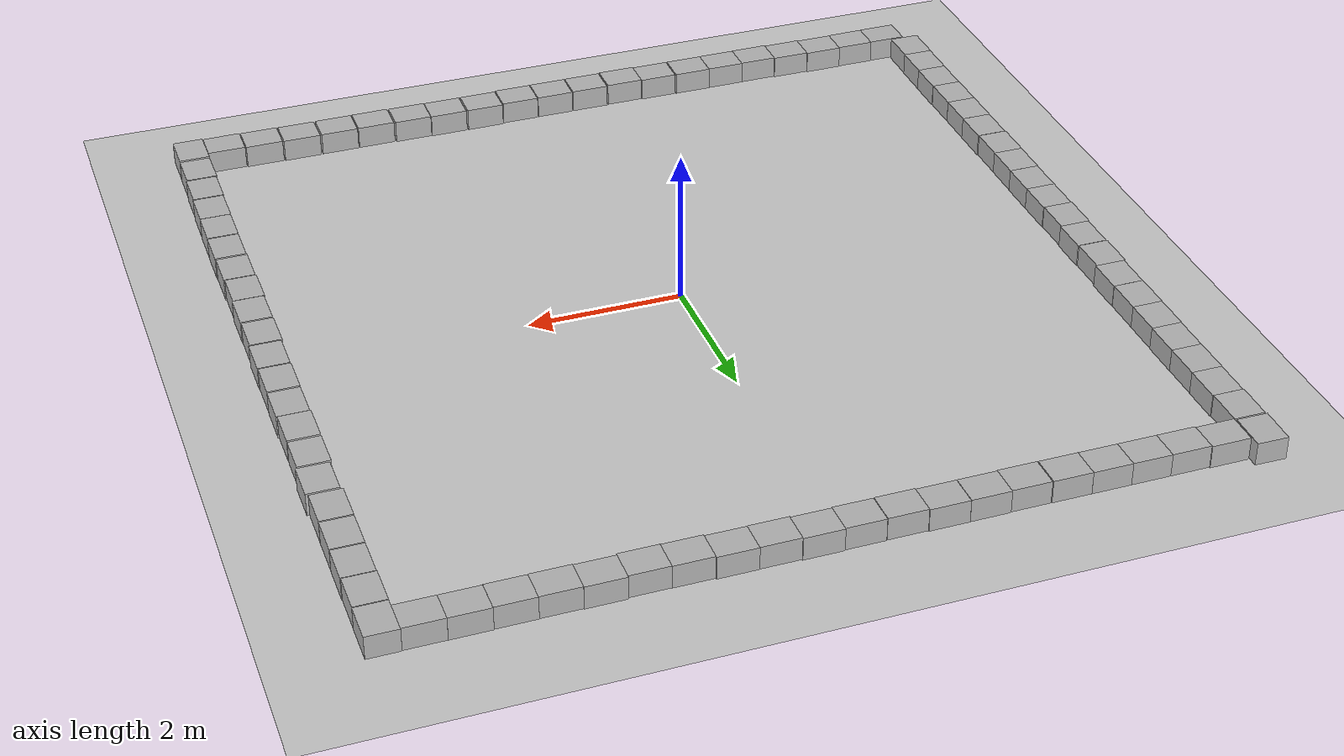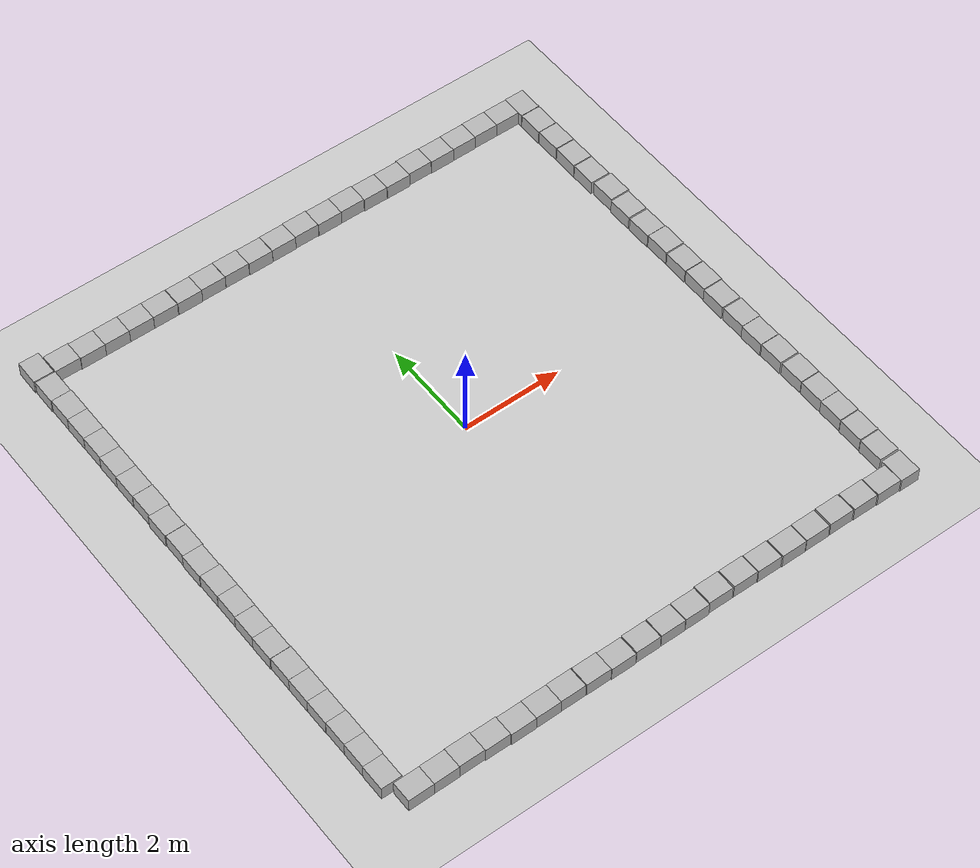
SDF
<sdf version="1.7">
 <world name="default">
  <light name="sun" type="directional">
   <pose>0 0 10 0 -0 0</pose>
   <diffuse>0.8 0.8 0.8 1</diffuse>
   <specular>0.2 0.2 0.2 1</specular>
   <attenuation>
    <range>1000</range>
    <constant>0.9</constant>
    <linear>0.01</linear>
    <quadratic>0.001</quadratic>
   </attenuation>
   <direction>-0.5 0.1 -0.9</direction>
   <spot><inner_angle>0</inner_angle><outer_angle>0</outer_angle><falloff>0</falloff></spot>
  </light>
  <model name="ground_plane">
   <static>1</static>
   <link name="link">
    <collision name="collision">
     <geometry><plane><normal>0 0 1</normal><size>100 100</size></plane></geometry>
     <surface>
      <contact><collide_bitmask>65535</collide_bitmask></contact>
      <friction><ode><mu>100</mu><mu2>50</mu2></ode></friction>
     </surface>
    </collision>
    <visual name="visual">
     <cast_shadows>0</cast_shadows>
     <geometry><plane><normal>0 0 1</normal><size>100 100</size></plane></geometry>
     <material>
      <script><uri>file://media/materials/scripts/gazebo.material</uri><name>Gazebo/Grey</name></script>
     </material>
    </visual>
   </link>
  </model>
  <gravity>0 0 -9.8</gravity>
  <magnetic_field>6e-06 2.3e-05 -4.2e-05</magnetic_field>
  <atmosphere type="adiabatic"/>
  <physics type="ode">
   <max_step_size>0.001</max_step_size>
   <real_time_factor>1</real_time_factor>
   <real_time_update_rate>1000</real_time_update_rate>
  </physics>
  <scene><ambient>0.4 0.4 0.4 1</ambient><background>0.7 0.7 0.7 1</background><shadows>1</shadows></scene>
  <audio><device>default</device></audio>
  <spherical_coordinates>
   <surface_model>EARTH_WGS84</surface_model>
   <latitude_deg>0</latitude_deg>
   <longitude_deg>0</longitude_deg>
   <elevation>0</elevation>
   <heading_deg>0</heading_deg>
  </spherical_coordinates>
  <model name="cardboard_box">
   <pose>5.20797 5.16251 0.149 0 0 -1.57037</pose>
   <link name="link">
    <inertial>
     <mass>2</mass>
     <inertia>
      <ixx>0.0416667</ixx>
      <ixy>0</ixy>
      <ixz>0</ixz>
      <iyy>0.0566667</iyy>
      <iyz>0</iyz>
      <izz>0.0683333</izz>
     </inertia>
    </inertial>
    <collision name="collision">
     <geometry><box><size>0.5 0.4 0.3</size></box></geometry>
     <surface>
      <friction><ode><mu>1</mu><mu2>1</mu2></ode></friction>
      <contact><ode><kp>1e+07</kp><kd>1</kd><min_depth>0.001</min_depth><max_vel>0.1</max_vel></ode></contact>
     </surface>
    </collision>
    <visual name="visual">
     <pose>0 0 -0.15 0 -0 0</pose>
     <geometry>
      <mesh><uri>model://cardboard_box/meshes/cardboard_box.dae</uri><scale>1.25932 1.00745 0.755591</scale></mesh>
     </geometry>
    </visual>
   </link>
  </model>
  <model name="cardboard_box_clone_0">
   <pose>4.75812 5.20518 0.149 0 -0 5.5e-05</pose>
   <link name="link">
    <inertial>
     <mass>2</mass>
     <inertia>
      <ixx>0.0416667</ixx>
      <ixy>0</ixy>
      <ixz>0</ixz>
      <iyy>0.0566667</iyy>
      <iyz>0</iyz>
      <izz>0.0683333</izz>
     </inertia>
    </inertial>
    <collision name="collision">
     <geometry><box><size>0.5 0.4 0.3</size></box></geometry>
     <surface>
      <friction><ode><mu>1</mu><mu2>1</mu2></ode></friction>
      <contact><ode><kp>1e+07</kp><kd>1</kd><min_depth>0.001</min_depth><max_vel>0.1</max_vel></ode></contact>
     </surface>
    </collision>
    <visual name="visual">
     <pose>0 0 -0.15 0 -0 0</pose>
     <geometry>
      <mesh><uri>model://cardboard_box/meshes/cardboard_box.dae</uri><scale>1.25932 1.00745 0.755591</scale></mesh>
     </geometry>
    </visual>
   </link>
  </model>
  <model name="cardboard_box_clone">
   <pose>5.20585 4.65107 0.149 0 0 -1.57145</pose>
   <link name="link">
    <inertial>
     <mass>2</mass>
     <inertia>
      <ixx>0.0416667</ixx>
      <ixy>0</ixy>
      <ixz>0</ixz>
      <iyy>0.0566667</iyy>
      <iyz>0</iyz>
      <izz>0.0683333</izz>
     </inertia>
    </inertial>
    <collision name="collision">
     <geometry><box><size>0.5 0.4 0.3</size></box></geometry>
     <surface>
      <friction><ode><mu>1</mu><mu2>1</mu2></ode></friction>
      <contact><ode><kp>1e+07</kp><kd>1</kd><min_depth>0.001</min_depth><max_vel>0.1</max_vel></ode></contact>
     </surface>
    </collision>
    <visual name="visual">
     <pose>0 0 -0.15 0 -0 0</pose>
     <geometry>
      <mesh><uri>model://cardboard_box/meshes/cardboard_box.dae</uri><scale>1.25932 1.00745 0.755591</scale></mesh>
     </geometry>
    </visual>
   </link>
  </model>
  <model name="cardboard_box_clone_1">
   <pose>5.21075 4.14182 0.149 0 0 -1.57145</pose>
   <link name="link">
    <inertial>
     <mass>2</mass>
     <inertia>
      <ixx>0.0416667</ixx>
      <ixy>0</ixy>
      <ixz>0</ixz>
      <iyy>0.0566667</iyy>
      <iyz>0</iyz>
      <izz>0.0683333</izz>
     </inertia>
    </inertial>
    <collision name="collision">
     <geometry><box><size>0.5 0.4 0.3</size></box></geometry>
     <surface>
      <friction><ode><mu>1</mu><mu2>1</mu2></ode></friction>
      <contact><ode><kp>1e+07</kp><kd>1</kd><min_depth>0.001</min_depth><max_vel>0.1</max_vel></ode></contact>
     </surface>
    </collision>
    <visual name="visual">
     <pose>0 0 -0.15 0 -0 0</pose>
     <geometry>
      <mesh><uri>model://cardboard_box/meshes/cardboard_box.dae</uri><scale>1.25932 1.00745 0.755591</scale></mesh>
     </geometry>
    </visual>
   </link>
  </model>
  <model name="cardboard_box_clone_2">
   <pose>5.20912 3.62631 0.149 0 0 -1.57145</pose>
   <link name="link">
    <inertial>
     <mass>2</mass>
     <inertia>
      <ixx>0.0416667</ixx>
      <ixy>0</ixy>
      <ixz>0</ixz>
      <iyy>0.0566667</iyy>
      <iyz>0</iyz>
      <izz>0.0683333</izz>
     </inertia>
    </inertial>
    <collision name="collision">
     <geometry><box><size>0.5 0.4 0.3</size></box></geometry>
     <surface>
      <friction><ode><mu>1</mu><mu2>1</mu2></ode></friction>
      <contact><ode><kp>1e+07</kp><kd>1</kd><min_depth>0.001</min_depth><max_vel>0.1</max_vel></ode></contact>
     </surface>
    </collision>
    <visual name="visual">
     <pose>0 0 -0.15 0 -0 0</pose>
     <geometry>
      <mesh><uri>model://cardboard_box/meshes/cardboard_box.dae</uri><scale>1.25932 1.00745 0.755591</scale></mesh>
     </geometry>
    </visual>
   </link>
  </model>
  <model name="cardboard_box_clone_3">
   <pose>5.20747 3.10773 0.149 0 0 -1.57145</pose>
   <link name="link">
    <inertial>
     <mass>2</mass>
     <inertia>
      <ixx>0.0416667</ixx>
      <ixy>0</ixy>
      <ixz>0</ixz>
      <iyy>0.0566667</iyy>
      <iyz>0</iyz>
      <izz>0.0683333</izz>
     </inertia>
    </inertial>
    <collision name="collision">
     <geometry><box><size>0.5 0.4 0.3</size></box></geometry>
     <surface>
      <friction><ode><mu>1</mu><mu2>1</mu2></ode></friction>
      <contact><ode><kp>1e+07</kp><kd>1</kd><min_depth>0.001</min_depth><max_vel>0.1</max_vel></ode></contact>
     </surface>
    </collision>
    <visual name="visual">
     <pose>0 0 -0.15 0 -0 0</pose>
     <geometry>
      <mesh><uri>model://cardboard_box/meshes/cardboard_box.dae</uri><scale>1.25932 1.00745 0.755591</scale></mesh>
     </geometry>
    </visual>
   </link>
  </model>
  <model name="cardboard_box_clone_0_clone">
   <pose>4.7419 -5.22507 0.149 0 -0 0</pose>
   <link name="link">
    <inertial>
     <mass>2</mass>
     <inertia>
      <ixx>0.0416667</ixx>
      <ixy>0</ixy>
      <ixz>0</ixz>
      <iyy>0.0566667</iyy>
      <iyz>0</iyz>
      <izz>0.0683333</izz>
     </inertia>
    </inertial>
    <collision name="collision">
     <geometry><box><size>0.5 0.4 0.3</size></box></geometry>
     <surface>
      <friction><ode><mu>1</mu><mu2>1</mu2></ode></friction>
      <contact><ode><kp>1e+07</kp><kd>1</kd><min_depth>0.001</min_depth><max_vel>0.1</max_vel></ode></contact>
     </surface>
    </collision>
    <visual name="visual">
     <pose>0 0 -0.15 0 -0 0</pose>
     <geometry>
      <mesh><uri>model://cardboard_box/meshes/cardboard_box.dae</uri><scale>1.25932 1.00745 0.755591</scale></mesh>
     </geometry>
    </visual>
   </link>
  </model>
  <model name="cardboard_box_clone_3_clone">
   <pose>5.23714 2.581 0.149 0 0 -1.57059</pose>
   <link name="link">
    <inertial>
     <mass>2</mass>
     <inertia>
      <ixx>0.0416667</ixx>
      <ixy>0</ixy>
      <ixz>0</ixz>
      <iyy>0.0566667</iyy>
      <iyz>0</iyz>
      <izz>0.0683333</izz>
     </inertia>
    </inertial>
    <collision name="collision">
     <geometry><box><size>0.5 0.4 0.3</size></box></geometry>
     <surface>
      <friction><ode><mu>1</mu><mu2>1</mu2></ode></friction>
      <contact><ode><kp>1e+07</kp><kd>1</kd><min_depth>0.001</min_depth><max_vel>0.1</max_vel></ode></contact>
     </surface>
    </collision>
    <visual name="visual">
     <pose>0 0 -0.15 0 -0 0</pose>
     <geometry>
      <mesh><uri>model://cardboard_box/meshes/cardboard_box.dae</uri><scale>1.25932 1.00745 0.755591</scale></mesh>
     </geometry>
    </visual>
   </link>
  </model>
  <model name="cardboard_box_clone_3_clone_0">
   <pose>5.21488 2.0557 0.149 -0 -0 -1.57057</pose>
   <link name="link">
    <inertial>
     <mass>2</mass>
     <inertia>
      <ixx>0.0416667</ixx>
      <ixy>0</ixy>
      <ixz>0</ixz>
      <iyy>0.0566667</iyy>
      <iyz>0</iyz>
      <izz>0.0683333</izz>
     </inertia>
    </inertial>
    <collision name="collision">
     <geometry><box><size>0.5 0.4 0.3</size></box></geometry>
     <surface>
      <friction><ode><mu>1</mu><mu2>1</mu2></ode></friction>
      <contact><ode><kp>1e+07</kp><kd>1</kd><min_depth>0.001</min_depth><max_vel>0.1</max_vel></ode></contact>
     </surface>
    </collision>
    <visual name="visual">
     <pose>0 0 -0.15 0 -0 0</pose>
     <geometry>
      <mesh><uri>model://cardboard_box/meshes/cardboard_box.dae</uri><scale>1.25932 1.00745 0.755591</scale></mesh>
     </geometry>
    </visual>
   </link>
  </model>
  <model name="cardboard_box_clone_3_clone_1">
   <pose>5.21446 1.52585 0.149 0 0 -1.57083</pose>
   <link name="link">
    <inertial>
     <mass>2</mass>
     <inertia>
      <ixx>0.0416667</ixx>
      <ixy>0</ixy>
      <ixz>0</ixz>
      <iyy>0.0566667</iyy>
      <iyz>0</iyz>
      <izz>0.0683333</izz>
     </inertia>
    </inertial>
    <collision name="collision">
     <geometry><box><size>0.5 0.4 0.3</size></box></geometry>
     <surface>
      <friction><ode><mu>1</mu><mu2>1</mu2></ode></friction>
      <contact><ode><kp>1e+07</kp><kd>1</kd><min_depth>0.001</min_depth><max_vel>0.1</max_vel></ode></contact>
     </surface>
    </collision>
    <visual name="visual">
     <pose>0 0 -0.15 0 -0 0</pose>
     <geometry>
      <mesh><uri>model://cardboard_box/meshes/cardboard_box.dae</uri><scale>1.25932 1.00745 0.755591</scale></mesh>
     </geometry>
    </visual>
   </link>
  </model>
  <model name="cardboard_box_clone_3_clone_2">
   <pose>5.22751 1.02138 0.149 0 -0 -1.57082</pose>
   <link name="link">
    <inertial>
     <mass>2</mass>
     <inertia>
      <ixx>0.0416667</ixx>
      <ixy>0</ixy>
      <ixz>0</ixz>
      <iyy>0.0566667</iyy>
      <iyz>0</iyz>
      <izz>0.0683333</izz>
     </inertia>
    </inertial>
    <collision name="collision">
     <geometry><box><size>0.5 0.4 0.3</size></box></geometry>
     <surface>
      <friction><ode><mu>1</mu><mu2>1</mu2></ode></friction>
      <contact><ode><kp>1e+07</kp><kd>1</kd><min_depth>0.001</min_depth><max_vel>0.1</max_vel></ode></contact>
     </surface>
    </collision>
    <visual name="visual">
     <pose>0 0 -0.15 0 -0 0</pose>
     <geometry>
      <mesh><uri>model://cardboard_box/meshes/cardboard_box.dae</uri><scale>1.25932 1.00745 0.755591</scale></mesh>
     </geometry>
    </visual>
   </link>
  </model>
  <model name="cardboard_box_clone_3_clone_3">
   <pose>5.22362 0.496907 0.149 -0 -0 -1.57095</pose>
   <link name="link">
    <inertial>
     <mass>2</mass>
     <inertia>
      <ixx>0.0416667</ixx>
      <ixy>0</ixy>
      <ixz>0</ixz>
      <iyy>0.0566667</iyy>
      <iyz>0</iyz>
      <izz>0.0683333</izz>
     </inertia>
    </inertial>
    <collision name="collision">
     <geometry><box><size>0.5 0.4 0.3</size></box></geometry>
     <surface>
      <friction><ode><mu>1</mu><mu2>1</mu2></ode></friction>
      <contact><ode><kp>1e+07</kp><kd>1</kd><min_depth>0.001</min_depth><max_vel>0.1</max_vel></ode></contact>
     </surface>
    </collision>
    <visual name="visual">
     <pose>0 0 -0.15 0 -0 0</pose>
     <geometry>
      <mesh><uri>model://cardboard_box/meshes/cardboard_box.dae</uri><scale>1.25932 1.00745 0.755591</scale></mesh>
     </geometry>
    </visual>
   </link>
  </model>
  <model name="cardboard_box_clone_3_clone_4">
   <pose>5.22941 -0.017542 0.149 -0 -0 -1.57145</pose>
   <link name="link">
    <inertial>
     <mass>2</mass>
     <inertia>
      <ixx>0.0416667</ixx>
      <ixy>0</ixy>
      <ixz>0</ixz>
      <iyy>0.0566667</iyy>
      <iyz>0</iyz>
      <izz>0.0683333</izz>
     </inertia>
    </inertial>
    <collision name="collision">
     <geometry><box><size>0.5 0.4 0.3</size></box></geometry>
     <surface>
      <friction><ode><mu>1</mu><mu2>1</mu2></ode></friction>
      <contact><ode><kp>1e+07</kp><kd>1</kd><min_depth>0.001</min_depth><max_vel>0.1</max_vel></ode></contact>
     </surface>
    </collision>
    <visual name="visual">
     <pose>0 0 -0.15 0 -0 0</pose>
     <geometry>
      <mesh><uri>model://cardboard_box/meshes/cardboard_box.dae</uri><scale>1.25932 1.00745 0.755591</scale></mesh>
     </geometry>
    </visual>
   </link>
  </model>
  <model name="cardboard_box_clone_3_clone_5">
   <pose>5.21393 -0.534657 0.149 0 0 -1.57145</pose>
   <link name="link">
    <inertial>
     <mass>2</mass>
     <inertia>
      <ixx>0.0416667</ixx>
      <ixy>0</ixy>
      <ixz>0</ixz>
      <iyy>0.0566667</iyy>
      <iyz>0</iyz>
      <izz>0.0683333</izz>
     </inertia>
    </inertial>
    <collision name="collision">
     <geometry><box><size>0.5 0.4 0.3</size></box></geometry>
     <surface>
      <friction><ode><mu>1</mu><mu2>1</mu2></ode></friction>
      <contact><ode><kp>1e+07</kp><kd>1</kd><min_depth>0.001</min_depth><max_vel>0.1</max_vel></ode></contact>
     </surface>
    </collision>
    <visual name="visual">
     <pose>0 0 -0.15 0 -0 0</pose>
     <geometry>
      <mesh><uri>model://cardboard_box/meshes/cardboard_box.dae</uri><scale>1.25932 1.00745 0.755591</scale></mesh>
     </geometry>
    </visual>
   </link>
  </model>
  <model name="cardboard_box_clone_3_clone_6">
   <pose>5.22011 -1.0587 0.149 0 0 -1.56968</pose>
   <link name="link">
    <inertial>
     <mass>2</mass>
     <inertia>
      <ixx>0.0416667</ixx>
      <ixy>0</ixy>
      <ixz>0</ixz>
      <iyy>0.0566667</iyy>
      <iyz>0</iyz>
      <izz>0.0683333</izz>
     </inertia>
    </inertial>
    <collision name="collision">
     <geometry><box><size>0.5 0.4 0.3</size></box></geometry>
     <surface>
      <friction><ode><mu>1</mu><mu2>1</mu2></ode></friction>
      <contact><ode><kp>1e+07</kp><kd>1</kd><min_depth>0.001</min_depth><max_vel>0.1</max_vel></ode></contact>
     </surface>
    </collision>
    <visual name="visual">
     <pose>0 0 -0.15 0 -0 0</pose>
     <geometry>
      <mesh><uri>model://cardboard_box/meshes/cardboard_box.dae</uri><scale>1.25932 1.00745 0.755591</scale></mesh>
     </geometry>
    </visual>
   </link>
  </model>
  <model name="cardboard_box_clone_3_clone_7">
   <pose>5.2103 -1.56434 0.149 -0 -0 -1.56968</pose>
   <link name="link">
    <inertial>
     <mass>2</mass>
     <inertia>
      <ixx>0.0416667</ixx>
      <ixy>0</ixy>
      <ixz>0</ixz>
      <iyy>0.0566667</iyy>
      <iyz>0</iyz>
      <izz>0.0683333</izz>
     </inertia>
    </inertial>
    <collision name="collision">
     <geometry><box><size>0.5 0.4 0.3</size></box></geometry>
     <surface>
      <friction><ode><mu>1</mu><mu2>1</mu2></ode></friction>
      <contact><ode><kp>1e+07</kp><kd>1</kd><min_depth>0.001</min_depth><max_vel>0.1</max_vel></ode></contact>
     </surface>
    </collision>
    <visual name="visual">
     <pose>0 0 -0.15 0 -0 0</pose>
     <geometry>
      <mesh><uri>model://cardboard_box/meshes/cardboard_box.dae</uri><scale>1.25932 1.00745 0.755591</scale></mesh>
     </geometry>
    </visual>
   </link>
  </model>
  <model name="cardboard_box_clone_3_clone_8">
   <pose>5.22199 -2.07455 0.149 0 -0 -1.57133</pose>
   <link name="link">
    <inertial>
     <mass>2</mass>
     <inertia>
      <ixx>0.0416667</ixx>
      <ixy>0</ixy>
      <ixz>0</ixz>
      <iyy>0.0566667</iyy>
      <iyz>0</iyz>
      <izz>0.0683333</izz>
     </inertia>
    </inertial>
    <collision name="collision">
     <geometry><box><size>0.5 0.4 0.3</size></box></geometry>
     <surface>
      <friction><ode><mu>1</mu><mu2>1</mu2></ode></friction>
      <contact><ode><kp>1e+07</kp><kd>1</kd><min_depth>0.001</min_depth><max_vel>0.1</max_vel></ode></contact>
     </surface>
    </collision>
    <visual name="visual">
     <pose>0 0 -0.15 0 -0 0</pose>
     <geometry>
      <mesh><uri>model://cardboard_box/meshes/cardboard_box.dae</uri><scale>1.25932 1.00745 0.755591</scale></mesh>
     </geometry>
    </visual>
   </link>
  </model>
  <model name="cardboard_box_clone_3_clone_9">
   <pose>5.22872 -2.60229 0.149 0 0 -1.57145</pose>
   <link name="link">
    <inertial>
     <mass>2</mass>
     <inertia>
      <ixx>0.0416667</ixx>
      <ixy>0</ixy>
      <ixz>0</ixz>
      <iyy>0.0566667</iyy>
      <iyz>0</iyz>
      <izz>0.0683333</izz>
     </inertia>
    </inertial>
    <collision name="collision">
     <geometry><box><size>0.5 0.4 0.3</size></box></geometry>
     <surface>
      <friction><ode><mu>1</mu><mu2>1</mu2></ode></friction>
      <contact><ode><kp>1e+07</kp><kd>1</kd><min_depth>0.001</min_depth><max_vel>0.1</max_vel></ode></contact>
     </surface>
    </collision>
    <visual name="visual">
     <pose>0 0 -0.15 0 -0 0</pose>
     <geometry>
      <mesh><uri>model://cardboard_box/meshes/cardboard_box.dae</uri><scale>1.25932 1.00745 0.755591</scale></mesh>
     </geometry>
    </visual>
   </link>
  </model>
  <model name="cardboard_box_clone_3_clone_10">
   <pose>5.22575 -3.11743 0.149 0 0 -1.57147</pose>
   <link name="link">
    <inertial>
     <mass>2</mass>
     <inertia>
      <ixx>0.0416667</ixx>
      <ixy>0</ixy>
      <ixz>0</ixz>
      <iyy>0.0566667</iyy>
      <iyz>0</iyz>
      <izz>0.0683333</izz>
     </inertia>
    </inertial>
    <collision name="collision">
     <geometry><box><size>0.5 0.4 0.3</size></box></geometry>
     <surface>
      <friction><ode><mu>1</mu><mu2>1</mu2></ode></friction>
      <contact><ode><kp>1e+07</kp><kd>1</kd><min_depth>0.001</min_depth><max_vel>0.1</max_vel></ode></contact>
     </surface>
    </collision>
    <visual name="visual">
     <pose>0 0 -0.15 0 -0 0</pose>
     <geometry>
      <mesh><uri>model://cardboard_box/meshes/cardboard_box.dae</uri><scale>1.25932 1.00745 0.755591</scale></mesh>
     </geometry>
    </visual>
   </link>
  </model>
  <model name="cardboard_box_clone_3_clone_11">
   <pose>5.22096 -3.62203 0.149 0 -0 -1.57143</pose>
   <link name="link">
    <inertial>
     <mass>2</mass>
     <inertia>
      <ixx>0.0416667</ixx>
      <ixy>0</ixy>
      <ixz>0</ixz>
      <iyy>0.0566667</iyy>
      <iyz>0</iyz>
      <izz>0.0683333</izz>
     </inertia>
    </inertial>
    <collision name="collision">
     <geometry><box><size>0.5 0.4 0.3</size></box></geometry>
     <surface>
      <friction><ode><mu>1</mu><mu2>1</mu2></ode></friction>
      <contact><ode><kp>1e+07</kp><kd>1</kd><min_depth>0.001</min_depth><max_vel>0.1</max_vel></ode></contact>
     </surface>
    </collision>
    <visual name="visual">
     <pose>0 0 -0.15 0 -0 0</pose>
     <geometry>
      <mesh><uri>model://cardboard_box/meshes/cardboard_box.dae</uri><scale>1.25932 1.00745 0.755591</scale></mesh>
     </geometry>
    </visual>
   </link>
  </model>
  <model name="cardboard_box_clone_3_clone_12">
   <pose>5.21202 -4.13807 0.149 -0 -0 -1.57142</pose>
   <link name="link">
    <inertial>
     <mass>2</mass>
     <inertia>
      <ixx>0.0416667</ixx>
      <ixy>0</ixy>
      <ixz>0</ixz>
      <iyy>0.0566667</iyy>
      <iyz>0</iyz>
      <izz>0.0683333</izz>
     </inertia>
    </inertial>
    <collision name="collision">
     <geometry><box><size>0.5 0.4 0.3</size></box></geometry>
     <surface>
      <friction><ode><mu>1</mu><mu2>1</mu2></ode></friction>
      <contact><ode><kp>1e+07</kp><kd>1</kd><min_depth>0.001</min_depth><max_vel>0.1</max_vel></ode></contact>
     </surface>
    </collision>
    <visual name="visual">
     <pose>0 0 -0.15 0 -0 0</pose>
     <geometry>
      <mesh><uri>model://cardboard_box/meshes/cardboard_box.dae</uri><scale>1.25932 1.00745 0.755591</scale></mesh>
     </geometry>
    </visual>
   </link>
  </model>
  <model name="cardboard_box_clone_3_clone_13">
   <pose>5.20127 -4.65492 0.149 0 0 -1.57145</pose>
   <link name="link">
    <inertial>
     <mass>2</mass>
     <inertia>
      <ixx>0.0416667</ixx>
      <ixy>0</ixy>
      <ixz>0</ixz>
      <iyy>0.0566667</iyy>
      <iyz>0</iyz>
      <izz>0.0683333</izz>
     </inertia>
    </inertial>
    <collision name="collision">
     <geometry><box><size>0.5 0.4 0.3</size></box></geometry>
     <surface>
      <friction><ode><mu>1</mu><mu2>1</mu2></ode></friction>
      <contact><ode><kp>1e+07</kp><kd>1</kd><min_depth>0.001</min_depth><max_vel>0.1</max_vel></ode></contact>
     </surface>
    </collision>
    <visual name="visual">
     <pose>0 0 -0.15 0 -0 0</pose>
     <geometry>
      <mesh><uri>model://cardboard_box/meshes/cardboard_box.dae</uri><scale>1.25932 1.00745 0.755591</scale></mesh>
     </geometry>
    </visual>
   </link>
  </model>
  <model name="cardboard_box_clone_3_clone_14">
   <pose>5.19711 -5.19229 0.149 0 0 -1.57145</pose>
   <link name="link">
    <inertial>
     <mass>2</mass>
     <inertia>
      <ixx>0.0416667</ixx>
      <ixy>0</ixy>
      <ixz>0</ixz>
      <iyy>0.0566667</iyy>
      <iyz>0</iyz>
      <izz>0.0683333</izz>
     </inertia>
    </inertial>
    <collision name="collision">
     <geometry><box><size>0.5 0.4 0.3</size></box></geometry>
     <surface>
      <friction><ode><mu>1</mu><mu2>1</mu2></ode></friction>
      <contact><ode><kp>1e+07</kp><kd>1</kd><min_depth>0.001</min_depth><max_vel>0.1</max_vel></ode></contact>
     </surface>
    </collision>
    <visual name="visual">
     <pose>0 0 -0.15 0 -0 0</pose>
     <geometry>
      <mesh><uri>model://cardboard_box/meshes/cardboard_box.dae</uri><scale>1.25932 1.00745 0.755591</scale></mesh>
     </geometry>
    </visual>
   </link>
  </model>
  <model name="cardboard_box_clone_0_clone_clone">
   <pose>-4.94789 -5.20823 0.149 0 -0 0.002209</pose>
   <link name="link">
    <inertial>
     <mass>2</mass>
     <inertia>
      <ixx>0.0416667</ixx>
      <ixy>0</ixy>
      <ixz>0</ixz>
      <iyy>0.0566667</iyy>
      <iyz>0</iyz>
      <izz>0.0683333</izz>
     </inertia>
    </inertial>
    <collision name="collision">
     <geometry><box><size>0.5 0.4 0.3</size></box></geometry>
     <surface>
      <friction><ode><mu>1</mu><mu2>1</mu2></ode></friction>
      <contact><ode><kp>1e+07</kp><kd>1</kd><min_depth>0.001</min_depth><max_vel>0.1</max_vel></ode></contact>
     </surface>
    </collision>
    <visual name="visual">
     <pose>0 0 -0.15 0 -0 0</pose>
     <geometry>
      <mesh><uri>model://cardboard_box/meshes/cardboard_box.dae</uri><scale>1.25932 1.00745 0.755591</scale></mesh>
     </geometry>
    </visual>
   </link>
  </model>
  <model name="cardboard_box_clone_0_clone_clone_1">
   <pose>4.22821 -5.21388 0.149 0 -0 0</pose>
   <link name="link">
    <inertial>
     <mass>2</mass>
     <inertia>
      <ixx>0.0416667</ixx>
      <ixy>0</ixy>
      <ixz>0</ixz>
      <iyy>0.0566667</iyy>
      <iyz>0</iyz>
      <izz>0.0683333</izz>
     </inertia>
    </inertial>
    <collision name="collision">
     <geometry><box><size>0.5 0.4 0.3</size></box></geometry>
     <surface>
      <friction><ode><mu>1</mu><mu2>1</mu2></ode></friction>
      <contact><ode><kp>1e+07</kp><kd>1</kd><min_depth>0.001</min_depth><max_vel>0.1</max_vel></ode></contact>
     </surface>
    </collision>
    <visual name="visual">
     <pose>0 0 -0.15 0 -0 0</pose>
     <geometry>
      <mesh><uri>model://cardboard_box/meshes/cardboard_box.dae</uri><scale>1.25932 1.00745 0.755591</scale></mesh>
     </geometry>
    </visual>
   </link>
  </model>
  <model name="cardboard_box_clone_0_clone_clone_1_clone">
   <pose>3.71067 -5.20506 0.149 0 -0 0</pose>
   <link name="link">
    <inertial>
     <mass>2</mass>
     <inertia>
      <ixx>0.0416667</ixx>
      <ixy>0</ixy>
      <ixz>0</ixz>
      <iyy>0.0566667</iyy>
      <iyz>0</iyz>
      <izz>0.0683333</izz>
     </inertia>
    </inertial>
    <collision name="collision">
     <geometry><box><size>0.5 0.4 0.3</size></box></geometry>
     <surface>
      <friction><ode><mu>1</mu><mu2>1</mu2></ode></friction>
      <contact><ode><kp>1e+07</kp><kd>1</kd><min_depth>0.001</min_depth><max_vel>0.1</max_vel></ode></contact>
     </surface>
    </collision>
    <visual name="visual">
     <pose>0 0 -0.15 0 -0 0</pose>
     <geometry>
      <mesh><uri>model://cardboard_box/meshes/cardboard_box.dae</uri><scale>1.25932 1.00745 0.755591</scale></mesh>
     </geometry>
    </visual>
   </link>
  </model>
  <model name="cardboard_box_clone_0_clone_clone_1_clone_clone">
   <pose>3.18585 -5.21037 0.149 0 -0 0</pose>
   <link name="link">
    <inertial>
     <mass>2</mass>
     <inertia>
      <ixx>0.0416667</ixx>
      <ixy>0</ixy>
      <ixz>0</ixz>
      <iyy>0.0566667</iyy>
      <iyz>0</iyz>
      <izz>0.0683333</izz>
     </inertia>
    </inertial>
    <collision name="collision">
     <geometry><box><size>0.5 0.4 0.3</size></box></geometry>
     <surface>
      <friction><ode><mu>1</mu><mu2>1</mu2></ode></friction>
      <contact><ode><kp>1e+07</kp><kd>1</kd><min_depth>0.001</min_depth><max_vel>0.1</max_vel></ode></contact>
     </surface>
    </collision>
    <visual name="visual">
     <pose>0 0 -0.15 0 -0 0</pose>
     <geometry>
      <mesh><uri>model://cardboard_box/meshes/cardboard_box.dae</uri><scale>1.25932 1.00745 0.755591</scale></mesh>
     </geometry>
    </visual>
   </link>
  </model>
  <model name="cardboard_box_clone_0_clone_clone_1_clone_clone_0">
   <pose>2.67264 -5.21412 0.149 0 -0 0</pose>
   <link name="link">
    <inertial>
     <mass>2</mass>
     <inertia>
      <ixx>0.0416667</ixx>
      <ixy>0</ixy>
      <ixz>0</ixz>
      <iyy>0.0566667</iyy>
      <iyz>0</iyz>
      <izz>0.0683333</izz>
     </inertia>
    </inertial>
    <collision name="collision">
     <geometry><box><size>0.5 0.4 0.3</size></box></geometry>
     <surface>
      <friction><ode><mu>1</mu><mu2>1</mu2></ode></friction>
      <contact><ode><kp>1e+07</kp><kd>1</kd><min_depth>0.001</min_depth><max_vel>0.1</max_vel></ode></contact>
     </surface>
    </collision>
    <visual name="visual">
     <pose>0 0 -0.15 0 -0 0</pose>
     <geometry>
      <mesh><uri>model://cardboard_box/meshes/cardboard_box.dae</uri><scale>1.25932 1.00745 0.755591</scale></mesh>
     </geometry>
    </visual>
   </link>
  </model>
  <model name="cardboard_box_clone_0_clone_clone_1_clone_clone_1">
   <pose>2.15125 -5.20314 0.149 0 -0 0</pose>
   <link name="link">
    <inertial>
     <mass>2</mass>
     <inertia>
      <ixx>0.0416667</ixx>
      <ixy>0</ixy>
      <ixz>0</ixz>
      <iyy>0.0566667</iyy>
      <iyz>0</iyz>
      <izz>0.0683333</izz>
     </inertia>
    </inertial>
    <collision name="collision">
     <geometry><box><size>0.5 0.4 0.3</size></box></geometry>
     <surface>
      <friction><ode><mu>1</mu><mu2>1</mu2></ode></friction>
      <contact><ode><kp>1e+07</kp><kd>1</kd><min_depth>0.001</min_depth><max_vel>0.1</max_vel></ode></contact>
     </surface>
    </collision>
    <visual name="visual">
     <pose>0 0 -0.15 0 -0 0</pose>
     <geometry>
      <mesh><uri>model://cardboard_box/meshes/cardboard_box.dae</uri><scale>1.25932 1.00745 0.755591</scale></mesh>
     </geometry>
    </visual>
   </link>
  </model>
  <model name="cardboard_box_clone_0_clone_clone_1_clone_clone_2">
   <pose>1.64451 -5.19354 0.149 0 -0 0</pose>
   <link name="link">
    <inertial>
     <mass>2</mass>
     <inertia>
      <ixx>0.0416667</ixx>
      <ixy>0</ixy>
      <ixz>0</ixz>
      <iyy>0.0566667</iyy>
      <iyz>0</iyz>
      <izz>0.0683333</izz>
     </inertia>
    </inertial>
    <collision name="collision">
     <geometry><box><size>0.5 0.4 0.3</size></box></geometry>
     <surface>
      <friction><ode><mu>1</mu><mu2>1</mu2></ode></friction>
      <contact><ode><kp>1e+07</kp><kd>1</kd><min_depth>0.001</min_depth><max_vel>0.1</max_vel></ode></contact>
     </surface>
    </collision>
    <visual name="visual">
     <pose>0 0 -0.15 0 -0 0</pose>
     <geometry>
      <mesh><uri>model://cardboard_box/meshes/cardboard_box.dae</uri><scale>1.25932 1.00745 0.755591</scale></mesh>
     </geometry>
    </visual>
   </link>
  </model>
  <model name="cardboard_box_clone_0_clone_clone_1_clone_clone_3">
   <pose>1.1225 -5.19279 0.149 0 -0 0</pose>
   <link name="link">
    <inertial>
     <mass>2</mass>
     <inertia>
      <ixx>0.0416667</ixx>
      <ixy>0</ixy>
      <ixz>0</ixz>
      <iyy>0.0566667</iyy>
      <iyz>0</iyz>
      <izz>0.0683333</izz>
     </inertia>
    </inertial>
    <collision name="collision">
     <geometry><box><size>0.5 0.4 0.3</size></box></geometry>
     <surface>
      <friction><ode><mu>1</mu><mu2>1</mu2></ode></friction>
      <contact><ode><kp>1e+07</kp><kd>1</kd><min_depth>0.001</min_depth><max_vel>0.1</max_vel></ode></contact>
     </surface>
    </collision>
    <visual name="visual">
     <pose>0 0 -0.15 0 -0 0</pose>
     <geometry>
      <mesh><uri>model://cardboard_box/meshes/cardboard_box.dae</uri><scale>1.25932 1.00745 0.755591</scale></mesh>
     </geometry>
    </visual>
   </link>
  </model>
  <model name="cardboard_box_clone_0_clone_clone_1_clone_clone_3_clone">
   <pose>0.607755 -5.21373 0.149 0 -0 0</pose>
   <link name="link">
    <inertial>
     <mass>2</mass>
     <inertia>
      <ixx>0.0416667</ixx>
      <ixy>0</ixy>
      <ixz>0</ixz>
      <iyy>0.0566667</iyy>
      <iyz>0</iyz>
      <izz>0.0683333</izz>
     </inertia>
    </inertial>
    <collision name="collision">
     <geometry><box><size>0.5 0.4 0.3</size></box></geometry>
     <surface>
      <friction><ode><mu>1</mu><mu2>1</mu2></ode></friction>
      <contact><ode><kp>1e+07</kp><kd>1</kd><min_depth>0.001</min_depth><max_vel>0.1</max_vel></ode></contact>
     </surface>
    </collision>
    <visual name="visual">
     <pose>0 0 -0.15 0 -0 0</pose>
     <geometry>
      <mesh><uri>model://cardboard_box/meshes/cardboard_box.dae</uri><scale>1.25932 1.00745 0.755591</scale></mesh>
     </geometry>
    </visual>
   </link>
  </model>
  <model name="cardboard_box_clone_0_clone_clone_1_clone_clone_3_clone_0">
   <pose>0.097509 -5.21699 0.149 0 -0 0</pose>
   <link name="link">
    <inertial>
     <mass>2</mass>
     <inertia>
      <ixx>0.0416667</ixx>
      <ixy>0</ixy>
      <ixz>0</ixz>
      <iyy>0.0566667</iyy>
      <iyz>0</iyz>
      <izz>0.0683333</izz>
     </inertia>
    </inertial>
    <collision name="collision">
     <geometry><box><size>0.5 0.4 0.3</size></box></geometry>
     <surface>
      <friction><ode><mu>1</mu><mu2>1</mu2></ode></friction>
      <contact><ode><kp>1e+07</kp><kd>1</kd><min_depth>0.001</min_depth><max_vel>0.1</max_vel></ode></contact>
     </surface>
    </collision>
    <visual name="visual">
     <pose>0 0 -0.15 0 -0 0</pose>
     <geometry>
      <mesh><uri>model://cardboard_box/meshes/cardboard_box.dae</uri><scale>1.25932 1.00745 0.755591</scale></mesh>
     </geometry>
    </visual>
   </link>
  </model>
  <model name="cardboard_box_clone_0_clone_clone_1_clone_clone_3_clone_1">
   <pose>-0.41726 -5.22028 0.149 0 -0 0</pose>
   <link name="link">
    <inertial>
     <mass>2</mass>
     <inertia>
      <ixx>0.0416667</ixx>
      <ixy>0</ixy>
      <ixz>0</ixz>
      <iyy>0.0566667</iyy>
      <iyz>0</iyz>
      <izz>0.0683333</izz>
     </inertia>
    </inertial>
    <collision name="collision">
     <geometry><box><size>0.5 0.4 0.3</size></box></geometry>
     <surface>
      <friction><ode><mu>1</mu><mu2>1</mu2></ode></friction>
      <contact><ode><kp>1e+07</kp><kd>1</kd><min_depth>0.001</min_depth><max_vel>0.1</max_vel></ode></contact>
     </surface>
    </collision>
    <visual name="visual">
     <pose>0 0 -0.15 0 -0 0</pose>
     <geometry>
      <mesh><uri>model://cardboard_box/meshes/cardboard_box.dae</uri><scale>1.25932 1.00745 0.755591</scale></mesh>
     </geometry>
    </visual>
   </link>
  </model>
  <model name="cardboard_box_clone_0_clone_clone_1_clone_clone_3_clone_2">
   <pose>-0.936489 -5.23317 0.149 -0 -0 -0.000377</pose>
   <link name="link">
    <inertial>
     <mass>2</mass>
     <inertia>
      <ixx>0.0416667</ixx>
      <ixy>0</ixy>
      <ixz>0</ixz>
      <iyy>0.0566667</iyy>
      <iyz>0</iyz>
      <izz>0.0683333</izz>
     </inertia>
    </inertial>
    <collision name="collision">
     <geometry><box><size>0.5 0.4 0.3</size></box></geometry>
     <surface>
      <friction><ode><mu>1</mu><mu2>1</mu2></ode></friction>
      <contact><ode><kp>1e+07</kp><kd>1</kd><min_depth>0.001</min_depth><max_vel>0.1</max_vel></ode></contact>
     </surface>
    </collision>
    <visual name="visual">
     <pose>0 0 -0.15 0 -0 0</pose>
     <geometry>
      <mesh><uri>model://cardboard_box/meshes/cardboard_box.dae</uri><scale>1.25932 1.00745 0.755591</scale></mesh>
     </geometry>
    </visual>
   </link>
  </model>
  <model name="cardboard_box_clone_0_clone_clone_1_clone_clone_3_clone_3">
   <pose>-1.43566 -5.21937 0.149 0 0 -0.000382</pose>
   <link name="link">
    <inertial>
     <mass>2</mass>
     <inertia>
      <ixx>0.0416667</ixx>
      <ixy>0</ixy>
      <ixz>0</ixz>
      <iyy>0.0566667</iyy>
      <iyz>0</iyz>
      <izz>0.0683333</izz>
     </inertia>
    </inertial>
    <collision name="collision">
     <geometry><box><size>0.5 0.4 0.3</size></box></geometry>
     <surface>
      <friction><ode><mu>1</mu><mu2>1</mu2></ode></friction>
      <contact><ode><kp>1e+07</kp><kd>1</kd><min_depth>0.001</min_depth><max_vel>0.1</max_vel></ode></contact>
     </surface>
    </collision>
    <visual name="visual">
     <pose>0 0 -0.15 0 -0 0</pose>
     <geometry>
      <mesh><uri>model://cardboard_box/meshes/cardboard_box.dae</uri><scale>1.25932 1.00745 0.755591</scale></mesh>
     </geometry>
    </visual>
   </link>
  </model>
  <model name="cardboard_box_clone_0_clone_clone_1_clone_clone_3_clone_3_clone">
   <pose>-1.95023 -5.21543 0.149 0 -0 0.000228</pose>
   <link name="link">
    <inertial>
     <mass>2</mass>
     <inertia>
      <ixx>0.0416667</ixx>
      <ixy>0</ixy>
      <ixz>0</ixz>
      <iyy>0.0566667</iyy>
      <iyz>0</iyz>
      <izz>0.0683333</izz>
     </inertia>
    </inertial>
    <collision name="collision">
     <geometry><box><size>0.5 0.4 0.3</size></box></geometry>
     <surface>
      <friction><ode><mu>1</mu><mu2>1</mu2></ode></friction>
      <contact><ode><kp>1e+07</kp><kd>1</kd><min_depth>0.001</min_depth><max_vel>0.1</max_vel></ode></contact>
     </surface>
    </collision>
    <visual name="visual">
     <pose>0 0 -0.15 0 -0 0</pose>
     <geometry>
      <mesh><uri>model://cardboard_box/meshes/cardboard_box.dae</uri><scale>1.25932 1.00745 0.755591</scale></mesh>
     </geometry>
    </visual>
   </link>
  </model>
  <model name="cardboard_box_clone_0_clone_clone_1_clone_clone_3_clone_3_clone_0">
   <pose>-2.45059 -5.22027 0.149 0 -0 0.000258</pose>
   <link name="link">
    <inertial>
     <mass>2</mass>
     <inertia>
      <ixx>0.0416667</ixx>
      <ixy>0</ixy>
      <ixz>0</ixz>
      <iyy>0.0566667</iyy>
      <iyz>0</iyz>
      <izz>0.0683333</izz>
     </inertia>
    </inertial>
    <collision name="collision">
     <geometry><box><size>0.5 0.4 0.3</size></box></geometry>
     <surface>
      <friction><ode><mu>1</mu><mu2>1</mu2></ode></friction>
      <contact><ode><kp>1e+07</kp><kd>1</kd><min_depth>0.001</min_depth><max_vel>0.1</max_vel></ode></contact>
     </surface>
    </collision>
    <visual name="visual">
     <pose>0 0 -0.15 0 -0 0</pose>
     <geometry>
      <mesh><uri>model://cardboard_box/meshes/cardboard_box.dae</uri><scale>1.25932 1.00745 0.755591</scale></mesh>
     </geometry>
    </visual>
   </link>
  </model>
  <model name="cardboard_box_clone_0_clone_clone_1_clone_clone_3_clone_3_clone_1">
   <pose>-2.95011 -5.22541 0.149 0 -0 0.000264</pose>
   <link name="link">
    <inertial>
     <mass>2</mass>
     <inertia>
      <ixx>0.0416667</ixx>
      <ixy>0</ixy>
      <ixz>0</ixz>
      <iyy>0.0566667</iyy>
      <iyz>0</iyz>
      <izz>0.0683333</izz>
     </inertia>
    </inertial>
    <collision name="collision">
     <geometry><box><size>0.5 0.4 0.3</size></box></geometry>
     <surface>
      <friction><ode><mu>1</mu><mu2>1</mu2></ode></friction>
      <contact><ode><kp>1e+07</kp><kd>1</kd><min_depth>0.001</min_depth><max_vel>0.1</max_vel></ode></contact>
     </surface>
    </collision>
    <visual name="visual">
     <pose>0 0 -0.15 0 -0 0</pose>
     <geometry>
      <mesh><uri>model://cardboard_box/meshes/cardboard_box.dae</uri><scale>1.25932 1.00745 0.755591</scale></mesh>
     </geometry>
    </visual>
   </link>
  </model>
  <model name="cardboard_box_clone_0_clone_clone_clone">
   <pose>-3.44946 -5.20833 0.149 0 -0 0.000859</pose>
   <link name="link">
    <inertial>
     <mass>2</mass>
     <inertia>
      <ixx>0.0416667</ixx>
      <ixy>0</ixy>
      <ixz>0</ixz>
      <iyy>0.0566667</iyy>
      <iyz>0</iyz>
      <izz>0.0683333</izz>
     </inertia>
    </inertial>
    <collision name="collision">
     <geometry><box><size>0.5 0.4 0.3</size></box></geometry>
     <surface>
      <friction><ode><mu>1</mu><mu2>1</mu2></ode></friction>
      <contact><ode><kp>1e+07</kp><kd>1</kd><min_depth>0.001</min_depth><max_vel>0.1</max_vel></ode></contact>
     </surface>
    </collision>
    <visual name="visual">
     <pose>0 0 -0.15 0 -0 0</pose>
     <geometry>
      <mesh><uri>model://cardboard_box/meshes/cardboard_box.dae</uri><scale>1.25932 1.00745 0.755591</scale></mesh>
     </geometry>
    </visual>
   </link>
  </model>
  <model name="cardboard_box_clone_0_clone_clone_clone_0">
   <pose>-3.94882 -5.19259 0.149 0 -0 0.002251</pose>
   <link name="link">
    <inertial>
     <mass>2</mass>
     <inertia>
      <ixx>0.0416667</ixx>
      <ixy>0</ixy>
      <ixz>0</ixz>
      <iyy>0.0566667</iyy>
      <iyz>0</iyz>
      <izz>0.0683333</izz>
     </inertia>
    </inertial>
    <collision name="collision">
     <geometry><box><size>0.5 0.4 0.3</size></box></geometry>
     <surface>
      <friction><ode><mu>1</mu><mu2>1</mu2></ode></friction>
      <contact><ode><kp>1e+07</kp><kd>1</kd><min_depth>0.001</min_depth><max_vel>0.1</max_vel></ode></contact>
     </surface>
    </collision>
    <visual name="visual">
     <pose>0 0 -0.15 0 -0 0</pose>
     <geometry>
      <mesh><uri>model://cardboard_box/meshes/cardboard_box.dae</uri><scale>1.25932 1.00745 0.755591</scale></mesh>
     </geometry>
    </visual>
   </link>
  </model>
  <model name="cardboard_box_clone_0_clone_clone_clone_1">
   <pose>-4.44793 -5.20311 0.149 0 -0 0.002209</pose>
   <link name="link">
    <inertial>
     <mass>2</mass>
     <inertia>
      <ixx>0.0416667</ixx>
      <ixy>0</ixy>
      <ixz>0</ixz>
      <iyy>0.0566667</iyy>
      <iyz>0</iyz>
      <izz>0.0683333</izz>
     </inertia>
    </inertial>
    <collision name="collision">
     <geometry><box><size>0.5 0.4 0.3</size></box></geometry>
     <surface>
      <friction><ode><mu>1</mu><mu2>1</mu2></ode></friction>
      <contact><ode><kp>1e+07</kp><kd>1</kd><min_depth>0.001</min_depth><max_vel>0.1</max_vel></ode></contact>
     </surface>
    </collision>
    <visual name="visual">
     <pose>0 0 -0.15 0 -0 0</pose>
     <geometry>
      <mesh><uri>model://cardboard_box/meshes/cardboard_box.dae</uri><scale>1.25932 1.00745 0.755591</scale></mesh>
     </geometry>
    </visual>
   </link>
  </model>
  <model name="cardboard_box_clone_3_clone_12_clone">
   <pose>-5.20941 -4.73302 0.149 0 -0 -1.57148</pose>
   <link name="link">
    <inertial>
     <mass>2</mass>
     <inertia>
      <ixx>0.0416667</ixx>
      <ixy>0</ixy>
      <ixz>0</ixz>
      <iyy>0.0566667</iyy>
      <iyz>0</iyz>
      <izz>0.0683333</izz>
     </inertia>
    </inertial>
    <collision name="collision">
     <geometry><box><size>0.5 0.4 0.3</size></box></geometry>
     <surface>
      <friction><ode><mu>1</mu><mu2>1</mu2></ode></friction>
      <contact><ode><kp>1e+07</kp><kd>1</kd><min_depth>0.001</min_depth><max_vel>0.1</max_vel></ode></contact>
     </surface>
    </collision>
    <visual name="visual">
     <pose>0 0 -0.15 0 -0 0</pose>
     <geometry>
      <mesh><uri>model://cardboard_box/meshes/cardboard_box.dae</uri><scale>1.25932 1.00745 0.755591</scale></mesh>
     </geometry>
    </visual>
   </link>
  </model>
  <model name="cardboard_box_clone_3_clone_12_clone_clone">
   <pose>-5.20275 -4.2337 0.149 0 0 -1.57134</pose>
   <link name="link">
    <inertial>
     <mass>2</mass>
     <inertia>
      <ixx>0.0416667</ixx>
      <ixy>0</ixy>
      <ixz>0</ixz>
      <iyy>0.0566667</iyy>
      <iyz>0</iyz>
      <izz>0.0683333</izz>
     </inertia>
    </inertial>
    <collision name="collision">
     <geometry><box><size>0.5 0.4 0.3</size></box></geometry>
     <surface>
      <friction><ode><mu>1</mu><mu2>1</mu2></ode></friction>
      <contact><ode><kp>1e+07</kp><kd>1</kd><min_depth>0.001</min_depth><max_vel>0.1</max_vel></ode></contact>
     </surface>
    </collision>
    <visual name="visual">
     <pose>0 0 -0.15 0 -0 0</pose>
     <geometry>
      <mesh><uri>model://cardboard_box/meshes/cardboard_box.dae</uri><scale>1.25932 1.00745 0.755591</scale></mesh>
     </geometry>
    </visual>
   </link>
  </model>
  <model name="cardboard_box_clone_3_clone_12_clone_clone_0">
   <pose>-5.2 -3.73449 0.149 -0 -0 -1.57147</pose>
   <link name="link">
    <inertial>
     <mass>2</mass>
     <inertia>
      <ixx>0.0416667</ixx>
      <ixy>0</ixy>
      <ixz>0</ixz>
      <iyy>0.0566667</iyy>
      <iyz>0</iyz>
      <izz>0.0683333</izz>
     </inertia>
    </inertial>
    <collision name="collision">
     <geometry><box><size>0.5 0.4 0.3</size></box></geometry>
     <surface>
      <friction><ode><mu>1</mu><mu2>1</mu2></ode></friction>
      <contact><ode><kp>1e+07</kp><kd>1</kd><min_depth>0.001</min_depth><max_vel>0.1</max_vel></ode></contact>
     </surface>
    </collision>
    <visual name="visual">
     <pose>0 0 -0.15 0 -0 0</pose>
     <geometry>
      <mesh><uri>model://cardboard_box/meshes/cardboard_box.dae</uri><scale>1.25932 1.00745 0.755591</scale></mesh>
     </geometry>
    </visual>
   </link>
  </model>
  <model name="cardboard_box_clone_3_clone_12_clone_clone_1">
   <pose>-5.20643 -3.23518 0.149 0 0 -1.57144</pose>
   <link name="link">
    <inertial>
     <mass>2</mass>
     <inertia>
      <ixx>0.0416667</ixx>
      <ixy>0</ixy>
      <ixz>0</ixz>
      <iyy>0.0566667</iyy>
      <iyz>0</iyz>
      <izz>0.0683333</izz>
     </inertia>
    </inertial>
    <collision name="collision">
     <geometry><box><size>0.5 0.4 0.3</size></box></geometry>
     <surface>
      <friction><ode><mu>1</mu><mu2>1</mu2></ode></friction>
      <contact><ode><kp>1e+07</kp><kd>1</kd><min_depth>0.001</min_depth><max_vel>0.1</max_vel></ode></contact>
     </surface>
    </collision>
    <visual name="visual">
     <pose>0 0 -0.15 0 -0 0</pose>
     <geometry>
      <mesh><uri>model://cardboard_box/meshes/cardboard_box.dae</uri><scale>1.25932 1.00745 0.755591</scale></mesh>
     </geometry>
    </visual>
   </link>
  </model>
  <model name="cardboard_box_clone_3_clone_12_clone_clone_1_clone">
   <pose>-5.20784 -2.73577 0.149 0 0 -1.57143</pose>
   <link name="link">
    <inertial>
     <mass>2</mass>
     <inertia>
      <ixx>0.0416667</ixx>
      <ixy>0</ixy>
      <ixz>0</ixz>
      <iyy>0.0566667</iyy>
      <iyz>0</iyz>
      <izz>0.0683333</izz>
     </inertia>
    </inertial>
    <collision name="collision">
     <geometry><box><size>0.5 0.4 0.3</size></box></geometry>
     <surface>
      <friction><ode><mu>1</mu><mu2>1</mu2></ode></friction>
      <contact><ode><kp>1e+07</kp><kd>1</kd><min_depth>0.001</min_depth><max_vel>0.1</max_vel></ode></contact>
     </surface>
    </collision>
    <visual name="visual">
     <pose>0 0 -0.15 0 -0 0</pose>
     <geometry>
      <mesh><uri>model://cardboard_box/meshes/cardboard_box.dae</uri><scale>1.25932 1.00745 0.755591</scale></mesh>
     </geometry>
    </visual>
   </link>
  </model>
  <model name="cardboard_box_clone_3_clone_12_clone_clone_1_clone_0">
   <pose>-5.2061 -2.23542 0.149 0 0 -1.57143</pose>
   <link name="link">
    <inertial>
     <mass>2</mass>
     <inertia>
      <ixx>0.0416667</ixx>
      <ixy>0</ixy>
      <ixz>0</ixz>
      <iyy>0.0566667</iyy>
      <iyz>0</iyz>
      <izz>0.0683333</izz>
     </inertia>
    </inertial>
    <collision name="collision">
     <geometry><box><size>0.5 0.4 0.3</size></box></geometry>
     <surface>
      <friction><ode><mu>1</mu><mu2>1</mu2></ode></friction>
      <contact><ode><kp>1e+07</kp><kd>1</kd><min_depth>0.001</min_depth><max_vel>0.1</max_vel></ode></contact>
     </surface>
    </collision>
    <visual name="visual">
     <pose>0 0 -0.15 0 -0 0</pose>
     <geometry>
      <mesh><uri>model://cardboard_box/meshes/cardboard_box.dae</uri><scale>1.25932 1.00745 0.755591</scale></mesh>
     </geometry>
    </visual>
   </link>
  </model>
  <model name="cardboard_box_clone_3_clone_12_clone_clone_1_clone_1">
   <pose>-5.21652 -1.72994 0.149 0 -0 -1.57143</pose>
   <link name="link">
    <inertial>
     <mass>2</mass>
     <inertia>
      <ixx>0.0416667</ixx>
      <ixy>0</ixy>
      <ixz>0</ixz>
      <iyy>0.0566667</iyy>
      <iyz>0</iyz>
      <izz>0.0683333</izz>
     </inertia>
    </inertial>
    <collision name="collision">
     <geometry><box><size>0.5 0.4 0.3</size></box></geometry>
     <surface>
      <friction><ode><mu>1</mu><mu2>1</mu2></ode></friction>
      <contact><ode><kp>1e+07</kp><kd>1</kd><min_depth>0.001</min_depth><max_vel>0.1</max_vel></ode></contact>
     </surface>
    </collision>
    <visual name="visual">
     <pose>0 0 -0.15 0 -0 0</pose>
     <geometry>
      <mesh><uri>model://cardboard_box/meshes/cardboard_box.dae</uri><scale>1.25932 1.00745 0.755591</scale></mesh>
     </geometry>
    </visual>
   </link>
  </model>
  <model name="cardboard_box_clone_3_clone_12_clone_clone_1_clone_2">
   <pose>-5.21377 -1.23076 0.149 0 0 -1.57143</pose>
   <link name="link">
    <inertial>
     <mass>2</mass>
     <inertia>
      <ixx>0.0416667</ixx>
      <ixy>0</ixy>
      <ixz>0</ixz>
      <iyy>0.0566667</iyy>
      <iyz>0</iyz>
      <izz>0.0683333</izz>
     </inertia>
    </inertial>
    <collision name="collision">
     <geometry><box><size>0.5 0.4 0.3</size></box></geometry>
     <surface>
      <friction><ode><mu>1</mu><mu2>1</mu2></ode></friction>
      <contact><ode><kp>1e+07</kp><kd>1</kd><min_depth>0.001</min_depth><max_vel>0.1</max_vel></ode></contact>
     </surface>
    </collision>
    <visual name="visual">
     <pose>0 0 -0.15 0 -0 0</pose>
     <geometry>
      <mesh><uri>model://cardboard_box/meshes/cardboard_box.dae</uri><scale>1.25932 1.00745 0.755591</scale></mesh>
     </geometry>
    </visual>
   </link>
  </model>
  <model name="cardboard_box_clone_3_clone_12_clone_clone_1_clone_3">
   <pose>-5.20957 -0.729667 0.149 0 -0 -1.57085</pose>
   <link name="link">
    <inertial>
     <mass>2</mass>
     <inertia>
      <ixx>0.0416667</ixx>
      <ixy>0</ixy>
      <ixz>0</ixz>
      <iyy>0.0566667</iyy>
      <iyz>0</iyz>
      <izz>0.0683333</izz>
     </inertia>
    </inertial>
    <collision name="collision">
     <geometry><box><size>0.5 0.4 0.3</size></box></geometry>
     <surface>
      <friction><ode><mu>1</mu><mu2>1</mu2></ode></friction>
      <contact><ode><kp>1e+07</kp><kd>1</kd><min_depth>0.001</min_depth><max_vel>0.1</max_vel></ode></contact>
     </surface>
    </collision>
    <visual name="visual">
     <pose>0 0 -0.15 0 -0 0</pose>
     <geometry>
      <mesh><uri>model://cardboard_box/meshes/cardboard_box.dae</uri><scale>1.25932 1.00745 0.755591</scale></mesh>
     </geometry>
    </visual>
   </link>
  </model>
  <model name="cardboard_box_clone_3_clone_12_clone_clone_1_clone_4">
   <pose>-5.21071 -0.23029 0.149 0 0 -1.57081</pose>
   <link name="link">
    <inertial>
     <mass>2</mass>
     <inertia>
      <ixx>0.0416667</ixx>
      <ixy>0</ixy>
      <ixz>0</ixz>
      <iyy>0.0566667</iyy>
      <iyz>0</iyz>
      <izz>0.0683333</izz>
     </inertia>
    </inertial>
    <collision name="collision">
     <geometry><box><size>0.5 0.4 0.3</size></box></geometry>
     <surface>
      <friction><ode><mu>1</mu><mu2>1</mu2></ode></friction>
      <contact><ode><kp>1e+07</kp><kd>1</kd><min_depth>0.001</min_depth><max_vel>0.1</max_vel></ode></contact>
     </surface>
    </collision>
    <visual name="visual">
     <pose>0 0 -0.15 0 -0 0</pose>
     <geometry>
      <mesh><uri>model://cardboard_box/meshes/cardboard_box.dae</uri><scale>1.25932 1.00745 0.755591</scale></mesh>
     </geometry>
    </visual>
   </link>
  </model>
  <model name="cardboard_box_clone_3_clone_12_clone_clone_1_clone_5">
   <pose>-5.22101 0.269066 0.149 0 -0 -1.57092</pose>
   <link name="link">
    <inertial>
     <mass>2</mass>
     <inertia>
      <ixx>0.0416667</ixx>
      <ixy>0</ixy>
      <ixz>0</ixz>
      <iyy>0.0566667</iyy>
      <iyz>0</iyz>
      <izz>0.0683333</izz>
     </inertia>
    </inertial>
    <collision name="collision">
     <geometry><box><size>0.5 0.4 0.3</size></box></geometry>
     <surface>
      <friction><ode><mu>1</mu><mu2>1</mu2></ode></friction>
      <contact><ode><kp>1e+07</kp><kd>1</kd><min_depth>0.001</min_depth><max_vel>0.1</max_vel></ode></contact>
     </surface>
    </collision>
    <visual name="visual">
     <pose>0 0 -0.15 0 -0 0</pose>
     <geometry>
      <mesh><uri>model://cardboard_box/meshes/cardboard_box.dae</uri><scale>1.25932 1.00745 0.755591</scale></mesh>
     </geometry>
    </visual>
   </link>
  </model>
  <model name="cardboard_box_clone_3_clone_12_clone_clone_1_clone_5_clone">
   <pose>-5.20919 0.768373 0.149 0 0 -1.57092</pose>
   <link name="link">
    <inertial>
     <mass>2</mass>
     <inertia>
      <ixx>0.0416667</ixx>
      <ixy>0</ixy>
      <ixz>0</ixz>
      <iyy>0.0566667</iyy>
      <iyz>0</iyz>
      <izz>0.0683333</izz>
     </inertia>
    </inertial>
    <collision name="collision">
     <geometry><box><size>0.5 0.4 0.3</size></box></geometry>
     <surface>
      <friction><ode><mu>1</mu><mu2>1</mu2></ode></friction>
      <contact><ode><kp>1e+07</kp><kd>1</kd><min_depth>0.001</min_depth><max_vel>0.1</max_vel></ode></contact>
     </surface>
    </collision>
    <visual name="visual">
     <pose>0 0 -0.15 0 -0 0</pose>
     <geometry>
      <mesh><uri>model://cardboard_box/meshes/cardboard_box.dae</uri><scale>1.25932 1.00745 0.755591</scale></mesh>
     </geometry>
    </visual>
   </link>
  </model>
  <model name="cardboard_box_clone_3_clone_12_clone_clone_1_clone_5_clone_0">
   <pose>-5.22042 1.27408 0.149 0 -0 -1.5714</pose>
   <link name="link">
    <inertial>
     <mass>2</mass>
     <inertia>
      <ixx>0.0416667</ixx>
      <ixy>0</ixy>
      <ixz>0</ixz>
      <iyy>0.0566667</iyy>
      <iyz>0</iyz>
      <izz>0.0683333</izz>
     </inertia>
    </inertial>
    <collision name="collision">
     <geometry><box><size>0.5 0.4 0.3</size></box></geometry>
     <surface>
      <friction><ode><mu>1</mu><mu2>1</mu2></ode></friction>
      <contact><ode><kp>1e+07</kp><kd>1</kd><min_depth>0.001</min_depth><max_vel>0.1</max_vel></ode></contact>
     </surface>
    </collision>
    <visual name="visual">
     <pose>0 0 -0.15 0 -0 0</pose>
     <geometry>
      <mesh><uri>model://cardboard_box/meshes/cardboard_box.dae</uri><scale>1.25932 1.00745 0.755591</scale></mesh>
     </geometry>
    </visual>
   </link>
  </model>
  <model name="cardboard_box_clone_3_clone_12_clone_clone_1_clone_5_clone_1">
   <pose>-5.20005 1.7737 0.149 0 0 -1.57099</pose>
   <link name="link">
    <inertial>
     <mass>2</mass>
     <inertia>
      <ixx>0.0416667</ixx>
      <ixy>0</ixy>
      <ixz>0</ixz>
      <iyy>0.0566667</iyy>
      <iyz>0</iyz>
      <izz>0.0683333</izz>
     </inertia>
    </inertial>
    <collision name="collision">
     <geometry><box><size>0.5 0.4 0.3</size></box></geometry>
     <surface>
      <friction><ode><mu>1</mu><mu2>1</mu2></ode></friction>
      <contact><ode><kp>1e+07</kp><kd>1</kd><min_depth>0.001</min_depth><max_vel>0.1</max_vel></ode></contact>
     </surface>
    </collision>
    <visual name="visual">
     <pose>0 0 -0.15 0 -0 0</pose>
     <geometry>
      <mesh><uri>model://cardboard_box/meshes/cardboard_box.dae</uri><scale>1.25932 1.00745 0.755591</scale></mesh>
     </geometry>
    </visual>
   </link>
  </model>
  <model name="cardboard_box_clone_3_clone_12_clone_clone_1_clone_5_clone_2">
   <pose>-5.20466 2.27451 0.149 -0 -0 -1.57084</pose>
   <link name="link">
    <inertial>
     <mass>2</mass>
     <inertia>
      <ixx>0.0416667</ixx>
      <ixy>0</ixy>
      <ixz>0</ixz>
      <iyy>0.0566667</iyy>
      <iyz>0</iyz>
      <izz>0.0683333</izz>
     </inertia>
    </inertial>
    <collision name="collision">
     <geometry><box><size>0.5 0.4 0.3</size></box></geometry>
     <surface>
      <friction><ode><mu>1</mu><mu2>1</mu2></ode></friction>
      <contact><ode><kp>1e+07</kp><kd>1</kd><min_depth>0.001</min_depth><max_vel>0.1</max_vel></ode></contact>
     </surface>
    </collision>
    <visual name="visual">
     <pose>0 0 -0.15 0 -0 0</pose>
     <geometry>
      <mesh><uri>model://cardboard_box/meshes/cardboard_box.dae</uri><scale>1.25932 1.00745 0.755591</scale></mesh>
     </geometry>
    </visual>
   </link>
  </model>
  <model name="cardboard_box_clone_3_clone_12_clone_clone_1_clone_5_clone_3">
   <pose>-5.20316 2.7746 0.149 0 -0 -1.57052</pose>
   <link name="link">
    <inertial>
     <mass>2</mass>
     <inertia>
      <ixx>0.0416667</ixx>
      <ixy>0</ixy>
      <ixz>0</ixz>
      <iyy>0.0566667</iyy>
      <iyz>0</iyz>
      <izz>0.0683333</izz>
     </inertia>
    </inertial>
    <collision name="collision">
     <geometry><box><size>0.5 0.4 0.3</size></box></geometry>
     <surface>
      <friction><ode><mu>1</mu><mu2>1</mu2></ode></friction>
      <contact><ode><kp>1e+07</kp><kd>1</kd><min_depth>0.001</min_depth><max_vel>0.1</max_vel></ode></contact>
     </surface>
    </collision>
    <visual name="visual">
     <pose>0 0 -0.15 0 -0 0</pose>
     <geometry>
      <mesh><uri>model://cardboard_box/meshes/cardboard_box.dae</uri><scale>1.25932 1.00745 0.755591</scale></mesh>
     </geometry>
    </visual>
   </link>
  </model>
  <model name="cardboard_box_clone_3_clone_12_clone_clone_1_clone_5_clone_4">
   <pose>-5.19813 3.27387 0.149 0 0 -1.57011</pose>
   <link name="link">
    <inertial>
     <mass>2</mass>
     <inertia>
      <ixx>0.0416667</ixx>
      <ixy>0</ixy>
      <ixz>0</ixz>
      <iyy>0.0566667</iyy>
      <iyz>0</iyz>
      <izz>0.0683333</izz>
     </inertia>
    </inertial>
    <collision name="collision">
     <geometry><box><size>0.5 0.4 0.3</size></box></geometry>
     <surface>
      <friction><ode><mu>1</mu><mu2>1</mu2></ode></friction>
      <contact><ode><kp>1e+07</kp><kd>1</kd><min_depth>0.001</min_depth><max_vel>0.1</max_vel></ode></contact>
     </surface>
    </collision>
    <visual name="visual">
     <pose>0 0 -0.15 0 -0 0</pose>
     <geometry>
      <mesh><uri>model://cardboard_box/meshes/cardboard_box.dae</uri><scale>1.25932 1.00745 0.755591</scale></mesh>
     </geometry>
    </visual>
   </link>
  </model>
  <model name="cardboard_box_clone_3_clone_12_clone_clone_1_clone_5_clone_5">
   <pose>-5.19993 3.77344 0.149 0 0 -1.56923</pose>
   <link name="link">
    <inertial>
     <mass>2</mass>
     <inertia>
      <ixx>0.0416667</ixx>
      <ixy>0</ixy>
      <ixz>0</ixz>
      <iyy>0.0566667</iyy>
      <iyz>0</iyz>
      <izz>0.0683333</izz>
     </inertia>
    </inertial>
    <collision name="collision">
     <geometry><box><size>0.5 0.4 0.3</size></box></geometry>
     <surface>
      <friction><ode><mu>1</mu><mu2>1</mu2></ode></friction>
      <contact><ode><kp>1e+07</kp><kd>1</kd><min_depth>0.001</min_depth><max_vel>0.1</max_vel></ode></contact>
     </surface>
    </collision>
    <visual name="visual">
     <pose>0 0 -0.15 0 -0 0</pose>
     <geometry>
      <mesh><uri>model://cardboard_box/meshes/cardboard_box.dae</uri><scale>1.25932 1.00745 0.755591</scale></mesh>
     </geometry>
    </visual>
   </link>
  </model>
  <model name="cardboard_box_clone_3_clone_12_clone_clone_1_clone_5_clone_6">
   <pose>-5.19779 4.27355 0.149 0 -0 -1.56997</pose>
   <link name="link">
    <inertial>
     <mass>2</mass>
     <inertia>
      <ixx>0.0416667</ixx>
      <ixy>0</ixy>
      <ixz>0</ixz>
      <iyy>0.0566667</iyy>
      <iyz>0</iyz>
      <izz>0.0683333</izz>
     </inertia>
    </inertial>
    <collision name="collision">
     <geometry><box><size>0.5 0.4 0.3</size></box></geometry>
     <surface>
      <friction><ode><mu>1</mu><mu2>1</mu2></ode></friction>
      <contact><ode><kp>1e+07</kp><kd>1</kd><min_depth>0.001</min_depth><max_vel>0.1</max_vel></ode></contact>
     </surface>
    </collision>
    <visual name="visual">
     <pose>0 0 -0.15 0 -0 0</pose>
     <geometry>
      <mesh><uri>model://cardboard_box/meshes/cardboard_box.dae</uri><scale>1.25932 1.00745 0.755591</scale></mesh>
     </geometry>
    </visual>
   </link>
  </model>
  <model name="cardboard_box_clone_3_clone_12_clone_clone_1_clone_5_clone_7">
   <pose>-5.20764 4.77393 0.149 0 0 -1.57685</pose>
   <link name="link">
    <inertial>
     <mass>2</mass>
     <inertia>
      <ixx>0.0416667</ixx>
      <ixy>0</ixy>
      <ixz>0</ixz>
      <iyy>0.0566667</iyy>
      <iyz>0</iyz>
      <izz>0.0683333</izz>
     </inertia>
    </inertial>
    <collision name="collision">
     <geometry><box><size>0.5 0.4 0.3</size></box></geometry>
     <surface>
      <friction><ode><mu>1</mu><mu2>1</mu2></ode></friction>
      <contact><ode><kp>1e+07</kp><kd>1</kd><min_depth>0.001</min_depth><max_vel>0.1</max_vel></ode></contact>
     </surface>
    </collision>
    <visual name="visual">
     <pose>0 0 -0.15 0 -0 0</pose>
     <geometry>
      <mesh><uri>model://cardboard_box/meshes/cardboard_box.dae</uri><scale>1.25932 1.00745 0.755591</scale></mesh>
     </geometry>
    </visual>
   </link>
  </model>
  <model name="cardboard_box_clone_3_clone_12_clone_clone_1_clone_5_clone_8">
   <pose>-5.21767 5.29456 0.149 0 0 -1.58605</pose>
   <link name="link">
    <inertial>
     <mass>2</mass>
     <inertia>
      <ixx>0.0416667</ixx>
      <ixy>0</ixy>
      <ixz>0</ixz>
      <iyy>0.0566667</iyy>
      <iyz>0</iyz>
      <izz>0.0683333</izz>
     </inertia>
    </inertial>
    <collision name="collision">
     <geometry><box><size>0.5 0.4 0.3</size></box></geometry>
     <surface>
      <friction><ode><mu>1</mu><mu2>1</mu2></ode></friction>
      <contact><ode><kp>1e+07</kp><kd>1</kd><min_depth>0.001</min_depth><max_vel>0.1</max_vel></ode></contact>
     </surface>
    </collision>
    <visual name="visual">
     <pose>0 0 -0.15 0 -0 0</pose>
     <geometry>
      <mesh><uri>model://cardboard_box/meshes/cardboard_box.dae</uri><scale>1.25932 1.00745 0.755591</scale></mesh>
     </geometry>
    </visual>
   </link>
  </model>
  <model name="cardboard_box_clone_0_clone_clone_1_clone_clone_3_clone_3_clone_0_clone">
   <pose>-4.75199 5.21666 0.149 0 -0 0.000103</pose>
   <link name="link">
    <inertial>
     <mass>2</mass>
     <inertia>
      <ixx>0.0416667</ixx>
      <ixy>0</ixy>
      <ixz>0</ixz>
      <iyy>0.0566667</iyy>
      <iyz>0</iyz>
      <izz>0.0683333</izz>
     </inertia>
    </inertial>
    <collision name="collision">
     <geometry><box><size>0.5 0.4 0.3</size></box></geometry>
     <surface>
      <friction><ode><mu>1</mu><mu2>1</mu2></ode></friction>
      <contact><ode><kp>1e+07</kp><kd>1</kd><min_depth>0.001</min_depth><max_vel>0.1</max_vel></ode></contact>
     </surface>
    </collision>
    <visual name="visual">
     <pose>0 0 -0.15 0 -0 0</pose>
     <geometry>
      <mesh><uri>model://cardboard_box/meshes/cardboard_box.dae</uri><scale>1.25932 1.00745 0.755591</scale></mesh>
     </geometry>
    </visual>
   </link>
  </model>
  <model name="cardboard_box_clone_0_clone_clone_1_clone_clone_3_clone_3_clone_0_clone_clone">
   <pose>-4.25241 5.20223 0.149 0 -0 0.000138</pose>
   <link name="link">
    <inertial>
     <mass>2</mass>
     <inertia>
      <ixx>0.0416667</ixx>
      <ixy>0</ixy>
      <ixz>0</ixz>
      <iyy>0.0566667</iyy>
      <iyz>0</iyz>
      <izz>0.0683333</izz>
     </inertia>
    </inertial>
    <collision name="collision">
     <geometry><box><size>0.5 0.4 0.3</size></box></geometry>
     <surface>
      <friction><ode><mu>1</mu><mu2>1</mu2></ode></friction>
      <contact><ode><kp>1e+07</kp><kd>1</kd><min_depth>0.001</min_depth><max_vel>0.1</max_vel></ode></contact>
     </surface>
    </collision>
    <visual name="visual">
     <pose>0 0 -0.15 0 -0 0</pose>
     <geometry>
      <mesh><uri>model://cardboard_box/meshes/cardboard_box.dae</uri><scale>1.25932 1.00745 0.755591</scale></mesh>
     </geometry>
    </visual>
   </link>
  </model>
  <model name="cardboard_box_clone_0_clone_clone_1_clone_clone_3_clone_3_clone_0_clone_clone_0">
   <pose>-3.75339 5.20287 0.149 0 -0 0.000191</pose>
   <link name="link">
    <inertial>
     <mass>2</mass>
     <inertia>
      <ixx>0.0416667</ixx>
      <ixy>0</ixy>
      <ixz>0</ixz>
      <iyy>0.0566667</iyy>
      <iyz>0</iyz>
      <izz>0.0683333</izz>
     </inertia>
    </inertial>
    <collision name="collision">
     <geometry><box><size>0.5 0.4 0.3</size></box></geometry>
     <surface>
      <friction><ode><mu>1</mu><mu2>1</mu2></ode></friction>
      <contact><ode><kp>1e+07</kp><kd>1</kd><min_depth>0.001</min_depth><max_vel>0.1</max_vel></ode></contact>
     </surface>
    </collision>
    <visual name="visual">
     <pose>0 0 -0.15 0 -0 0</pose>
     <geometry>
      <mesh><uri>model://cardboard_box/meshes/cardboard_box.dae</uri><scale>1.25932 1.00745 0.755591</scale></mesh>
     </geometry>
    </visual>
   </link>
  </model>
  <model name="cardboard_box_clone_0_clone_clone_1_clone_clone_3_clone_3_clone_0_clone_clone_1">
   <pose>-3.25391 5.20345 0.149 0 -0 0.000266</pose>
   <link name="link">
    <inertial>
     <mass>2</mass>
     <inertia>
      <ixx>0.0416667</ixx>
      <ixy>0</ixy>
      <ixz>0</ixz>
      <iyy>0.0566667</iyy>
      <iyz>0</iyz>
      <izz>0.0683333</izz>
     </inertia>
    </inertial>
    <collision name="collision">
     <geometry><box><size>0.5 0.4 0.3</size></box></geometry>
     <surface>
      <friction><ode><mu>1</mu><mu2>1</mu2></ode></friction>
      <contact><ode><kp>1e+07</kp><kd>1</kd><min_depth>0.001</min_depth><max_vel>0.1</max_vel></ode></contact>
     </surface>
    </collision>
    <visual name="visual">
     <pose>0 0 -0.15 0 -0 0</pose>
     <geometry>
      <mesh><uri>model://cardboard_box/meshes/cardboard_box.dae</uri><scale>1.25932 1.00745 0.755591</scale></mesh>
     </geometry>
    </visual>
   </link>
  </model>
  <model name="cardboard_box_clone_0_clone_clone_1_clone_clone_3_clone_3_clone_0_clone_clone_2">
   <pose>-2.7545 5.20218 0.149 0 -0 0.000272</pose>
   <link name="link">
    <inertial>
     <mass>2</mass>
     <inertia>
      <ixx>0.0416667</ixx>
      <ixy>0</ixy>
      <ixz>0</ixz>
      <iyy>0.0566667</iyy>
      <iyz>0</iyz>
      <izz>0.0683333</izz>
     </inertia>
    </inertial>
    <collision name="collision">
     <geometry><box><size>0.5 0.4 0.3</size></box></geometry>
     <surface>
      <friction><ode><mu>1</mu><mu2>1</mu2></ode></friction>
      <contact><ode><kp>1e+07</kp><kd>1</kd><min_depth>0.001</min_depth><max_vel>0.1</max_vel></ode></contact>
     </surface>
    </collision>
    <visual name="visual">
     <pose>0 0 -0.15 0 -0 0</pose>
     <geometry>
      <mesh><uri>model://cardboard_box/meshes/cardboard_box.dae</uri><scale>1.25932 1.00745 0.755591</scale></mesh>
     </geometry>
    </visual>
   </link>
  </model>
  <model name="cardboard_box_clone_0_clone_clone_1_clone_clone_3_clone_3_clone_0_clone_clone_2_clone">
   <pose>-2.24487 5.19947 0.149 0 -0 0.000272</pose>
   <link name="link">
    <inertial>
     <mass>2</mass>
     <inertia>
      <ixx>0.0416667</ixx>
      <ixy>0</ixy>
      <ixz>0</ixz>
      <iyy>0.0566667</iyy>
      <iyz>0</iyz>
      <izz>0.0683333</izz>
     </inertia>
    </inertial>
    <collision name="collision">
     <geometry><box><size>0.5 0.4 0.3</size></box></geometry>
     <surface>
      <friction><ode><mu>1</mu><mu2>1</mu2></ode></friction>
      <contact><ode><kp>1e+07</kp><kd>1</kd><min_depth>0.001</min_depth><max_vel>0.1</max_vel></ode></contact>
     </surface>
    </collision>
    <visual name="visual">
     <pose>0 0 -0.15 0 -0 0</pose>
     <geometry>
      <mesh><uri>model://cardboard_box/meshes/cardboard_box.dae</uri><scale>1.25932 1.00745 0.755591</scale></mesh>
     </geometry>
    </visual>
   </link>
  </model>
  <model name="cardboard_box_clone_0_clone_clone_1_clone_clone_3_clone_3_clone_0_clone_clone_2_clone_0">
   <pose>-1.74572 5.20828 0.149 0 -0 0.000272</pose>
   <link name="link">
    <inertial>
     <mass>2</mass>
     <inertia>
      <ixx>0.0416667</ixx>
      <ixy>0</ixy>
      <ixz>0</ixz>
      <iyy>0.0566667</iyy>
      <iyz>0</iyz>
      <izz>0.0683333</izz>
     </inertia>
    </inertial>
    <collision name="collision">
     <geometry><box><size>0.5 0.4 0.3</size></box></geometry>
     <surface>
      <friction><ode><mu>1</mu><mu2>1</mu2></ode></friction>
      <contact><ode><kp>1e+07</kp><kd>1</kd><min_depth>0.001</min_depth><max_vel>0.1</max_vel></ode></contact>
     </surface>
    </collision>
    <visual name="visual">
     <pose>0 0 -0.15 0 -0 0</pose>
     <geometry>
      <mesh><uri>model://cardboard_box/meshes/cardboard_box.dae</uri><scale>1.25932 1.00745 0.755591</scale></mesh>
     </geometry>
    </visual>
   </link>
  </model>
  <model name="cardboard_box_clone_0_clone_clone_1_clone_clone_3_clone_3_clone_0_clone_clone_2_clone_1">
   <pose>-1.24242 5.21096 0.149 0 -0 0.000272</pose>
   <link name="link">
    <inertial>
     <mass>2</mass>
     <inertia>
      <ixx>0.0416667</ixx>
      <ixy>0</ixy>
      <ixz>0</ixz>
      <iyy>0.0566667</iyy>
      <iyz>0</iyz>
      <izz>0.0683333</izz>
     </inertia>
    </inertial>
    <collision name="collision">
     <geometry><box><size>0.5 0.4 0.3</size></box></geometry>
     <surface>
      <friction><ode><mu>1</mu><mu2>1</mu2></ode></friction>
      <contact><ode><kp>1e+07</kp><kd>1</kd><min_depth>0.001</min_depth><max_vel>0.1</max_vel></ode></contact>
     </surface>
    </collision>
    <visual name="visual">
     <pose>0 0 -0.15 0 -0 0</pose>
     <geometry>
      <mesh><uri>model://cardboard_box/meshes/cardboard_box.dae</uri><scale>1.25932 1.00745 0.755591</scale></mesh>
     </geometry>
    </visual>
   </link>
  </model>
  <model name="cardboard_box_clone_0_clone_clone_1_clone_clone_3_clone_3_clone_0_clone_clone_2_clone_2">
   <pose>-0.743264 5.19859 0.149 0 -0 0.000272</pose>
   <link name="link">
    <inertial>
     <mass>2</mass>
     <inertia>
      <ixx>0.0416667</ixx>
      <ixy>0</ixy>
      <ixz>0</ixz>
      <iyy>0.0566667</iyy>
      <iyz>0</iyz>
      <izz>0.0683333</izz>
     </inertia>
    </inertial>
    <collision name="collision">
     <geometry><box><size>0.5 0.4 0.3</size></box></geometry>
     <surface>
      <friction><ode><mu>1</mu><mu2>1</mu2></ode></friction>
      <contact><ode><kp>1e+07</kp><kd>1</kd><min_depth>0.001</min_depth><max_vel>0.1</max_vel></ode></contact>
     </surface>
    </collision>
    <visual name="visual">
     <pose>0 0 -0.15 0 -0 0</pose>
     <geometry>
      <mesh><uri>model://cardboard_box/meshes/cardboard_box.dae</uri><scale>1.25932 1.00745 0.755591</scale></mesh>
     </geometry>
    </visual>
   </link>
  </model>
  <model name="cardboard_box_clone_0_clone_clone_1_clone_clone_3_clone_3_clone_0_clone_clone_2_clone_3">
   <pose>-0.237873 5.20443 0.149 0 0 -0.000728</pose>
   <link name="link">
    <inertial>
     <mass>2</mass>
     <inertia>
      <ixx>0.0416667</ixx>
      <ixy>0</ixy>
      <ixz>0</ixz>
      <iyy>0.0566667</iyy>
      <iyz>0</iyz>
      <izz>0.0683333</izz>
     </inertia>
    </inertial>
    <collision name="collision">
     <geometry><box><size>0.5 0.4 0.3</size></box></geometry>
     <surface>
      <friction><ode><mu>1</mu><mu2>1</mu2></ode></friction>
      <contact><ode><kp>1e+07</kp><kd>1</kd><min_depth>0.001</min_depth><max_vel>0.1</max_vel></ode></contact>
     </surface>
    </collision>
    <visual name="visual">
     <pose>0 0 -0.15 0 -0 0</pose>
     <geometry>
      <mesh><uri>model://cardboard_box/meshes/cardboard_box.dae</uri><scale>1.25932 1.00745 0.755591</scale></mesh>
     </geometry>
    </visual>
   </link>
  </model>
  <model name="cardboard_box_clone_0_clone_clone_1_clone_clone_3_clone_3_clone_0_clone_clone_2_clone_3_clone">
   <pose>0.261346 5.21523 0.149 0 -0 -0.000831</pose>
   <link name="link">
    <inertial>
     <mass>2</mass>
     <inertia>
      <ixx>0.0416667</ixx>
      <ixy>0</ixy>
      <ixz>0</ixz>
      <iyy>0.0566667</iyy>
      <iyz>0</iyz>
      <izz>0.0683333</izz>
     </inertia>
    </inertial>
    <collision name="collision">
     <geometry><box><size>0.5 0.4 0.3</size></box></geometry>
     <surface>
      <friction><ode><mu>1</mu><mu2>1</mu2></ode></friction>
      <contact><ode><kp>1e+07</kp><kd>1</kd><min_depth>0.001</min_depth><max_vel>0.1</max_vel></ode></contact>
     </surface>
    </collision>
    <visual name="visual">
     <pose>0 0 -0.15 0 -0 0</pose>
     <geometry>
      <mesh><uri>model://cardboard_box/meshes/cardboard_box.dae</uri><scale>1.25932 1.00745 0.755591</scale></mesh>
     </geometry>
    </visual>
   </link>
  </model>
  <model name="cardboard_box_clone_0_clone_clone_1_clone_clone_3_clone_3_clone_0_clone_clone_2_clone_3_clone_0">
   <pose>0.760475 5.20135 0.149 0 0 -0.000784</pose>
   <link name="link">
    <inertial>
     <mass>2</mass>
     <inertia>
      <ixx>0.0416667</ixx>
      <ixy>0</ixy>
      <ixz>0</ixz>
      <iyy>0.0566667</iyy>
      <iyz>0</iyz>
      <izz>0.0683333</izz>
     </inertia>
    </inertial>
    <collision name="collision">
     <geometry><box><size>0.5 0.4 0.3</size></box></geometry>
     <surface>
      <friction><ode><mu>1</mu><mu2>1</mu2></ode></friction>
      <contact><ode><kp>1e+07</kp><kd>1</kd><min_depth>0.001</min_depth><max_vel>0.1</max_vel></ode></contact>
     </surface>
    </collision>
    <visual name="visual">
     <pose>0 0 -0.15 0 -0 0</pose>
     <geometry>
      <mesh><uri>model://cardboard_box/meshes/cardboard_box.dae</uri><scale>1.25932 1.00745 0.755591</scale></mesh>
     </geometry>
    </visual>
   </link>
  </model>
  <model name="cardboard_box_clone_0_clone_clone_1_clone_clone_3_clone_3_clone_0_clone_clone_2_clone_3_clone_1">
   <pose>1.26016 5.20547 0.149 0 -0 -0.000707</pose>
   <link name="link">
    <inertial>
     <mass>2</mass>
     <inertia>
      <ixx>0.0416667</ixx>
      <ixy>0</ixy>
      <ixz>0</ixz>
      <iyy>0.0566667</iyy>
      <iyz>0</iyz>
      <izz>0.0683333</izz>
     </inertia>
    </inertial>
    <collision name="collision">
     <geometry><box><size>0.5 0.4 0.3</size></box></geometry>
     <surface>
      <friction><ode><mu>1</mu><mu2>1</mu2></ode></friction>
      <contact><ode><kp>1e+07</kp><kd>1</kd><min_depth>0.001</min_depth><max_vel>0.1</max_vel></ode></contact>
     </surface>
    </collision>
    <visual name="visual">
     <pose>0 0 -0.15 0 -0 0</pose>
     <geometry>
      <mesh><uri>model://cardboard_box/meshes/cardboard_box.dae</uri><scale>1.25932 1.00745 0.755591</scale></mesh>
     </geometry>
    </visual>
   </link>
  </model>
  <model name="cardboard_box_clone_0_clone_clone_1_clone_clone_3_clone_3_clone_0_clone_clone_2_clone_3_clone_1_clone">
   <pose>1.76013 5.18781 0.149 0 0 -0.000515</pose>
   <link name="link">
    <inertial>
     <mass>2</mass>
     <inertia>
      <ixx>0.0416667</ixx>
      <ixy>0</ixy>
      <ixz>0</ixz>
      <iyy>0.0566667</iyy>
      <iyz>0</iyz>
      <izz>0.0683333</izz>
     </inertia>
    </inertial>
    <collision name="collision">
     <geometry><box><size>0.5 0.4 0.3</size></box></geometry>
     <surface>
      <friction><ode><mu>1</mu><mu2>1</mu2></ode></friction>
      <contact><ode><kp>1e+07</kp><kd>1</kd><min_depth>0.001</min_depth><max_vel>0.1</max_vel></ode></contact>
     </surface>
    </collision>
    <visual name="visual">
     <pose>0 0 -0.15 0 -0 0</pose>
     <geometry>
      <mesh><uri>model://cardboard_box/meshes/cardboard_box.dae</uri><scale>1.25932 1.00745 0.755591</scale></mesh>
     </geometry>
    </visual>
   </link>
  </model>
  <model name="cardboard_box_clone_0_clone_clone_1_clone_clone_3_clone_3_clone_0_clone_clone_2_clone_3_clone_1_clone_0">
   <pose>2.25958 5.18214 0.149 -0 -0 -0.000291</pose>
   <link name="link">
    <inertial>
     <mass>2</mass>
     <inertia>
      <ixx>0.0416667</ixx>
      <ixy>0</ixy>
      <ixz>0</ixz>
      <iyy>0.0566667</iyy>
      <iyz>0</iyz>
      <izz>0.0683333</izz>
     </inertia>
    </inertial>
    <collision name="collision">
     <geometry><box><size>0.5 0.4 0.3</size></box></geometry>
     <surface>
      <friction><ode><mu>1</mu><mu2>1</mu2></ode></friction>
      <contact><ode><kp>1e+07</kp><kd>1</kd><min_depth>0.001</min_depth><max_vel>0.1</max_vel></ode></contact>
     </surface>
    </collision>
    <visual name="visual">
     <pose>0 0 -0.15 0 -0 0</pose>
     <geometry>
      <mesh><uri>model://cardboard_box/meshes/cardboard_box.dae</uri><scale>1.25932 1.00745 0.755591</scale></mesh>
     </geometry>
    </visual>
   </link>
  </model>
  <model name="cardboard_box_clone_0_clone_clone_1_clone_clone_3_clone_3_clone_0_clone_clone_2_clone_3_clone_1_clone_1">
   <pose>2.75869 5.20401 0.149 -0 -0 -0.000163</pose>
   <link name="link">
    <inertial>
     <mass>2</mass>
     <inertia>
      <ixx>0.0416667</ixx>
      <ixy>0</ixy>
      <ixz>0</ixz>
      <iyy>0.0566667</iyy>
      <iyz>0</iyz>
      <izz>0.0683333</izz>
     </inertia>
    </inertial>
    <collision name="collision">
     <geometry><box><size>0.5 0.4 0.3</size></box></geometry>
     <surface>
      <friction><ode><mu>1</mu><mu2>1</mu2></ode></friction>
      <contact><ode><kp>1e+07</kp><kd>1</kd><min_depth>0.001</min_depth><max_vel>0.1</max_vel></ode></contact>
     </surface>
    </collision>
    <visual name="visual">
     <pose>0 0 -0.15 0 -0 0</pose>
     <geometry>
      <mesh><uri>model://cardboard_box/meshes/cardboard_box.dae</uri><scale>1.25932 1.00745 0.755591</scale></mesh>
     </geometry>
    </visual>
   </link>
  </model>
  <model name="cardboard_box_clone_0_clone_clone_1_clone_clone_3_clone_3_clone_0_clone_clone_2_clone_3_clone_1_clone_2">
   <pose>3.25803 5.19443 0.149 0 0 -8.4e-05</pose>
   <link name="link">
    <inertial>
     <mass>2</mass>
     <inertia>
      <ixx>0.0416667</ixx>
      <ixy>0</ixy>
      <ixz>0</ixz>
      <iyy>0.0566667</iyy>
      <iyz>0</iyz>
      <izz>0.0683333</izz>
     </inertia>
    </inertial>
    <collision name="collision">
     <geometry><box><size>0.5 0.4 0.3</size></box></geometry>
     <surface>
      <friction><ode><mu>1</mu><mu2>1</mu2></ode></friction>
      <contact><ode><kp>1e+07</kp><kd>1</kd><min_depth>0.001</min_depth><max_vel>0.1</max_vel></ode></contact>
     </surface>
    </collision>
    <visual name="visual">
     <pose>0 0 -0.15 0 -0 0</pose>
     <geometry>
      <mesh><uri>model://cardboard_box/meshes/cardboard_box.dae</uri><scale>1.25932 1.00745 0.755591</scale></mesh>
     </geometry>
    </visual>
   </link>
  </model>
  <model name="cardboard_box_clone_0_clone_clone_1_clone_clone_3_clone_3_clone_0_clone_clone_2_clone_3_clone_1_clone_3">
   <pose>3.75798 5.19932 0.149 0 -0 -5.3e-05</pose>
   <link name="link">
    <inertial>
     <mass>2</mass>
     <inertia>
      <ixx>0.0416667</ixx>
      <ixy>0</ixy>
      <ixz>0</ixz>
      <iyy>0.0566667</iyy>
      <iyz>0</iyz>
      <izz>0.0683333</izz>
     </inertia>
    </inertial>
    <collision name="collision">
     <geometry><box><size>0.5 0.4 0.3</size></box></geometry>
     <surface>
      <friction><ode><mu>1</mu><mu2>1</mu2></ode></friction>
      <contact><ode><kp>1e+07</kp><kd>1</kd><min_depth>0.001</min_depth><max_vel>0.1</max_vel></ode></contact>
     </surface>
    </collision>
    <visual name="visual">
     <pose>0 0 -0.15 0 -0 0</pose>
     <geometry>
      <mesh><uri>model://cardboard_box/meshes/cardboard_box.dae</uri><scale>1.25932 1.00745 0.755591</scale></mesh>
     </geometry>
    </visual>
   </link>
  </model>
  <model name="cardboard_box_clone_0_clone_clone_1_clone_clone_3_clone_3_clone_0_clone_clone_2_clone_3_clone_1_clone_4">
   <pose>4.25826 5.20695 0.149 0 0 -0.000131</pose>
   <link name="link">
    <inertial>
     <mass>2</mass>
     <inertia>
      <ixx>0.0416667</ixx>
      <ixy>0</ixy>
      <ixz>0</ixz>
      <iyy>0.0566667</iyy>
      <iyz>0</iyz>
      <izz>0.0683333</izz>
     </inertia>
    </inertial>
    <collision name="collision">
     <geometry><box><size>0.5 0.4 0.3</size></box></geometry>
     <surface>
      <friction><ode><mu>1</mu><mu2>1</mu2></ode></friction>
      <contact><ode><kp>1e+07</kp><kd>1</kd><min_depth>0.001</min_depth><max_vel>0.1</max_vel></ode></contact>
     </surface>
    </collision>
    <visual name="visual">
     <pose>0 0 -0.15 0 -0 0</pose>
     <geometry>
      <mesh><uri>model://cardboard_box/meshes/cardboard_box.dae</uri><scale>1.25932 1.00745 0.755591</scale></mesh>
     </geometry>
    </visual>
   </link>
  </model>
 </world>
</sdf>
